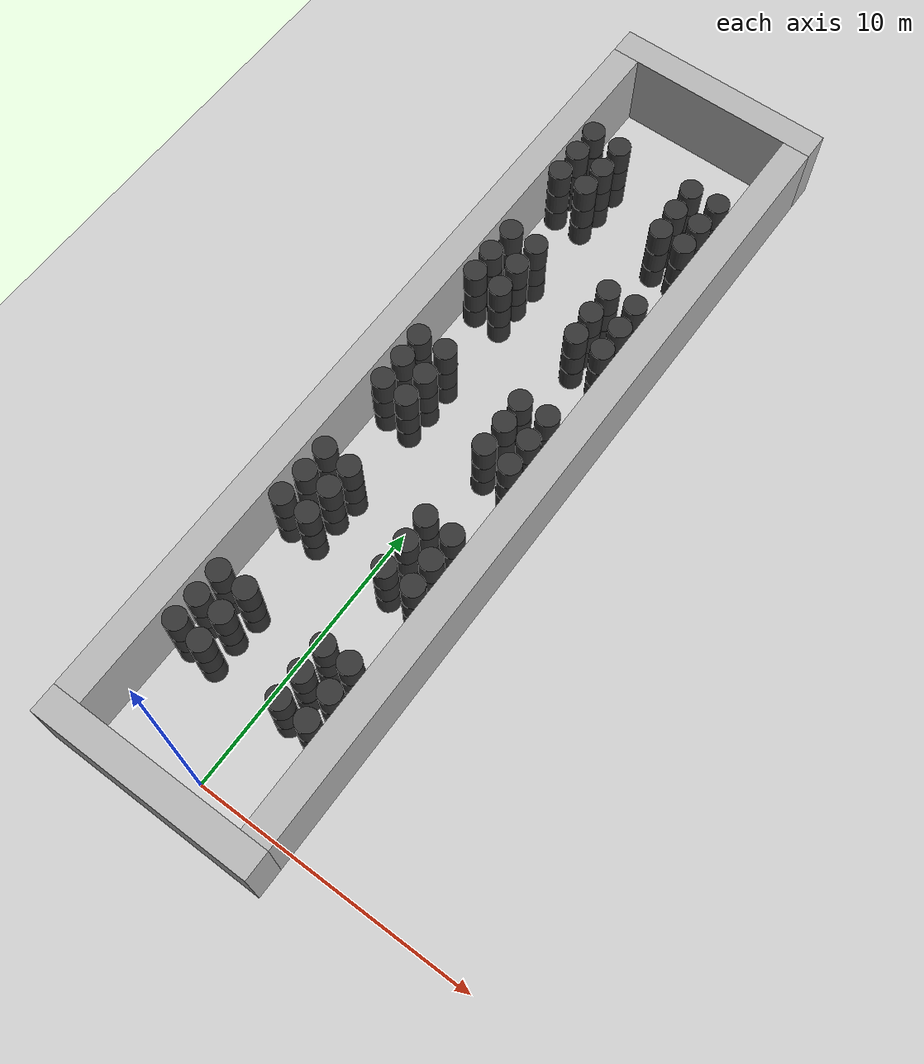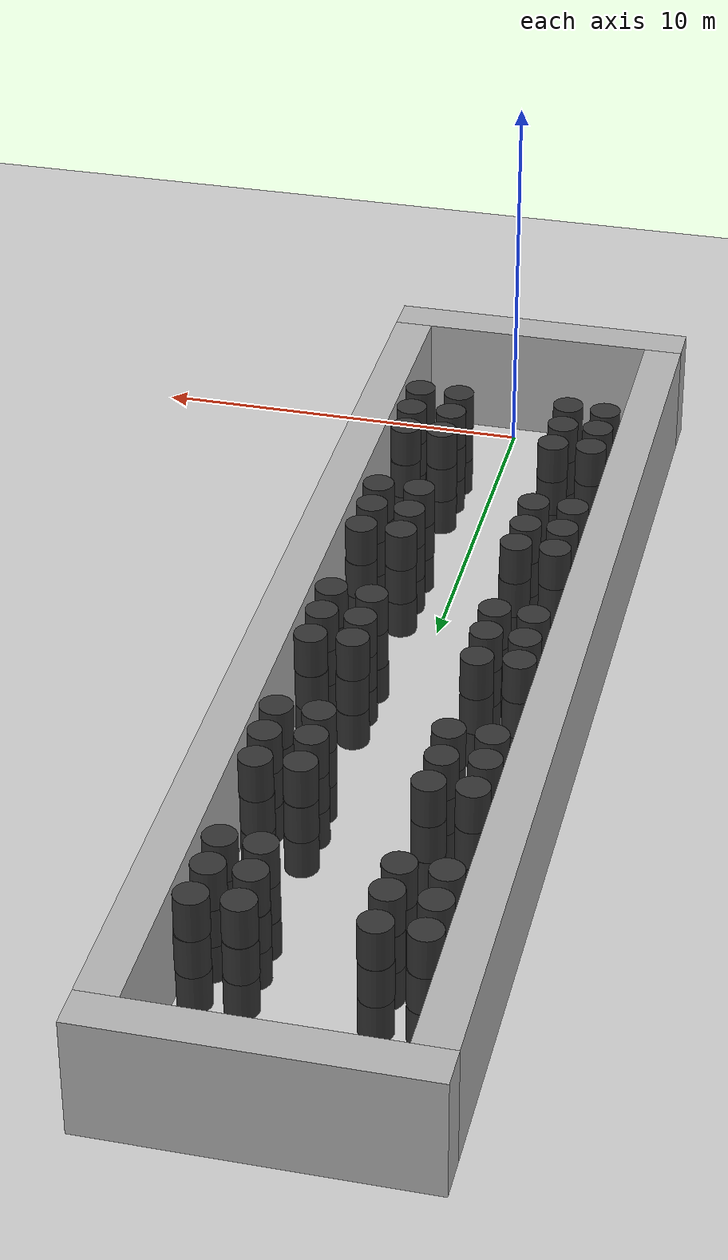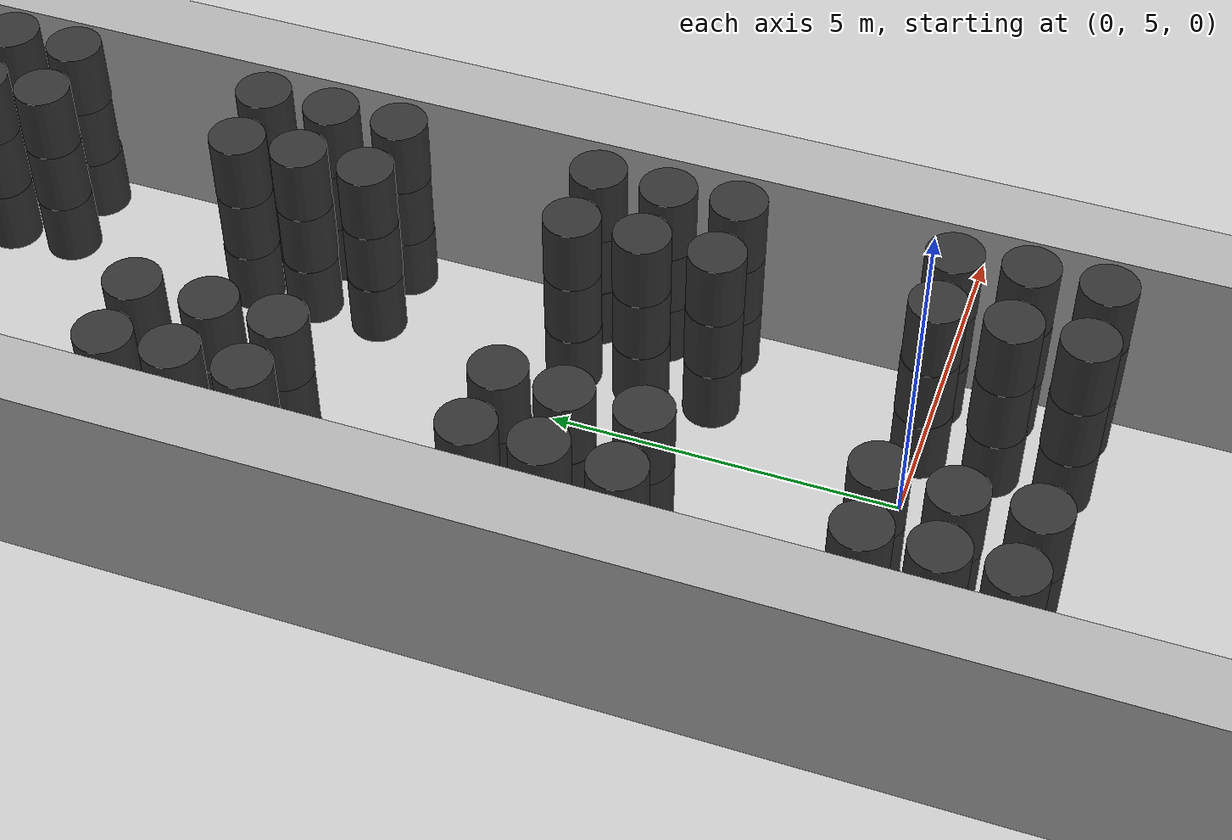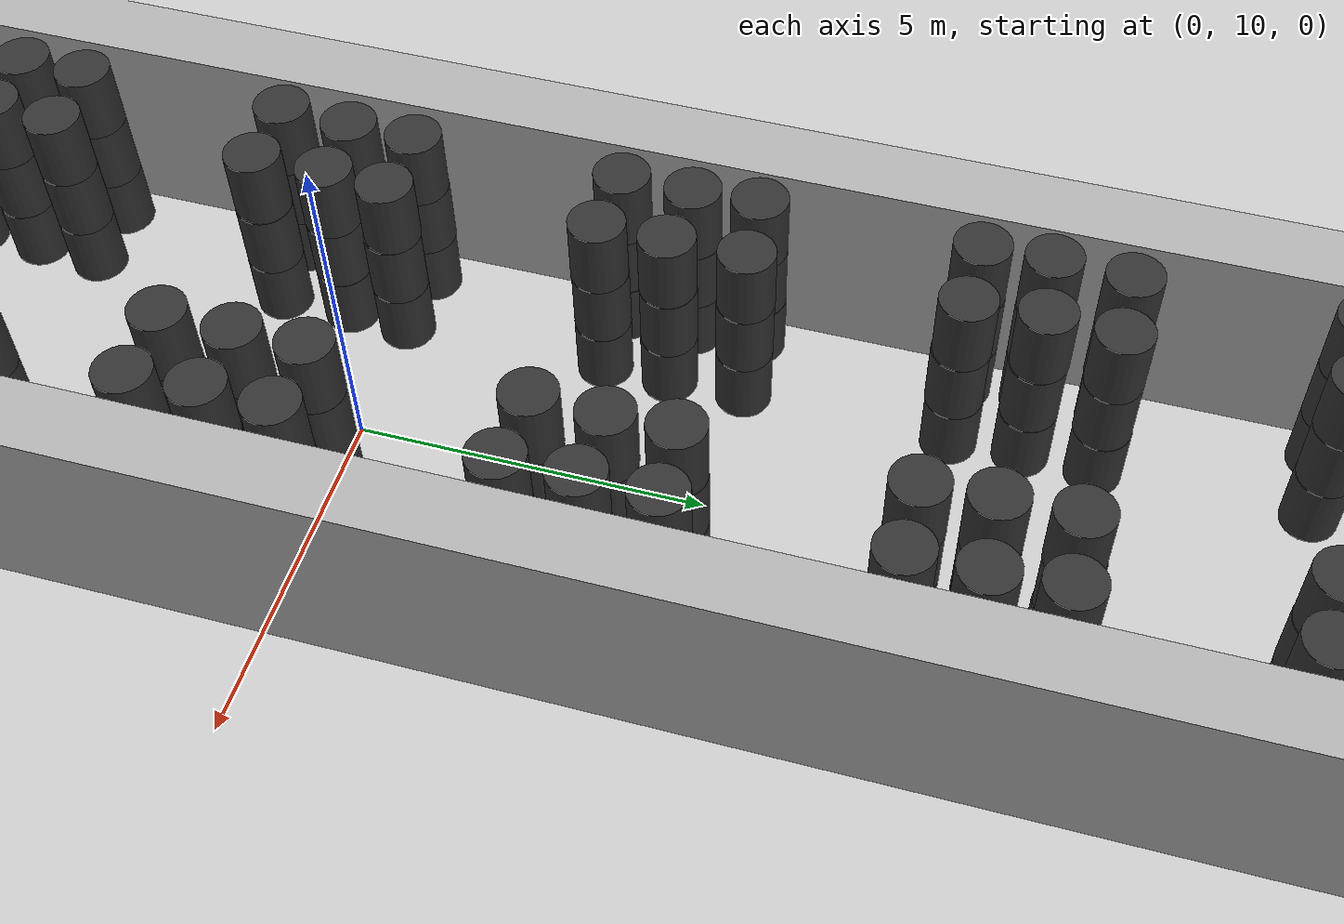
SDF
<sdf version="1.6">
 <world name="default">
  <light name="sun" type="directional">
   <cast_shadows>0</cast_shadows>
   <pose>0 0 10 0 -0 0</pose>
   <diffuse>0.8 0.8 0.8 1</diffuse>
   <specular>0.2 0.2 0.2 1</specular>
   <attenuation>
    <range>1000</range>
    <constant>0.9</constant>
    <linear>0.01</linear>
    <quadratic>0.001</quadratic>
   </attenuation>
   <direction>-0.5 0.1 -0.9</direction>
  </light>
  <include><uri>model://ground_plane</uri></include>
  <gravity>0 0 -9.8</gravity>
  <magnetic_field>6e-06 2.3e-05 -4.2e-05</magnetic_field>
  <atmosphere type="adiabatic"/>
  <physics default="0" name="default_physics" type="ode">
   <max_step_size>0.001</max_step_size>
   <real_time_factor>1</real_time_factor>
   <real_time_update_rate>1000</real_time_update_rate>
  </physics>
  <scene><ambient>0.4 0.4 0.4 1</ambient><background>0.7 0.7 0.7 1</background><shadows>0</shadows></scene>
  <spherical_coordinates>
   <surface_model>EARTH_WGS84</surface_model>
   <latitude_deg>0</latitude_deg>
   <longitude_deg>0</longitude_deg>
   <elevation>0</elevation>
   <heading_deg>0</heading_deg>
  </spherical_coordinates>
  <model name="wall_0">
   <pose frame="sim_world">-4.0 14.0 1.5 0 0 0</pose>
   <static>True</static>
   <link name="wall_0_link">
    <inertial>
     <mass>100</mass>
     <inertia>
      <ixx>0.166667</ixx>
      <ixy>0</ixy>
      <ixz>0</ixz>
      <iyy>0.166667</iyy>
      <iyz>0</iyz>
      <izz>0.166667</izz>
     </inertia>
    </inertial>
    <collision name="wall_0_collision">
     <geometry><box><size>1.0 29.0 3.0</size></box></geometry>
     <max_contacts>100</max_contacts>
    </collision>
    <visual name="wall_0_visual">
     <geometry><box><size>1.0 29.0 3.0</size></box></geometry>
     <material><ambient>0.7 0.7 0.7 1</ambient><diffuse>0.7 0.7 0.7 1</diffuse></material>
    </visual>
   </link>
  </model>
  <model name="wall_1">
   <pose frame="sim_world">3.0 14.0 1.5 0 0 0</pose>
   <static>True</static>
   <link name="wall_1_link">
    <inertial>
     <mass>100</mass>
     <inertia>
      <ixx>0.166667</ixx>
      <ixy>0</ixy>
      <ixz>0</ixz>
      <iyy>0.166667</iyy>
      <iyz>0</iyz>
      <izz>0.166667</izz>
     </inertia>
    </inertial>
    <collision name="wall_1_collision">
     <geometry><box><size>1.0 29.0 3.0</size></box></geometry>
     <max_contacts>100</max_contacts>
    </collision>
    <visual name="wall_1_visual">
     <geometry><box><size>1.0 29.0 3.0</size></box></geometry>
     <material><ambient>0.7 0.7 0.7 1</ambient><diffuse>0.7 0.7 0.7 1</diffuse></material>
    </visual>
   </link>
  </model>
  <model name="wall_2">
   <pose frame="sim_world">-0.5 -1.0 1.5 0 0 0</pose>
   <static>True</static>
   <link name="wall_2_link">
    <inertial>
     <mass>100</mass>
     <inertia>
      <ixx>0.166667</ixx>
      <ixy>0</ixy>
      <ixz>0</ixz>
      <iyy>0.166667</iyy>
      <iyz>0</iyz>
      <izz>0.166667</izz>
     </inertia>
    </inertial>
    <collision name="wall_2_collision">
     <geometry><box><size>8.0 1.0 3.0</size></box></geometry>
     <max_contacts>100</max_contacts>
    </collision>
    <visual name="wall_2_visual">
     <geometry><box><size>8.0 1.0 3.0</size></box></geometry>
     <material><ambient>0.7 0.7 0.7 1</ambient><diffuse>0.7 0.7 0.7 1</diffuse></material>
    </visual>
   </link>
  </model>
  <model name="wall_3">
   <pose frame="sim_world">-0.5 29.0 1.5 0 0 0</pose>
   <static>True</static>
   <link name="wall_3_link">
    <inertial>
     <mass>100</mass>
     <inertia>
      <ixx>0.166667</ixx>
      <ixy>0</ixy>
      <ixz>0</ixz>
      <iyy>0.166667</iyy>
      <iyz>0</iyz>
      <izz>0.166667</izz>
     </inertia>
    </inertial>
    <collision name="wall_3_collision">
     <geometry><box><size>8.0 1.0 3.0</size></box></geometry>
     <max_contacts>100</max_contacts>
    </collision>
    <visual name="wall_3_visual">
     <geometry><box><size>8.0 1.0 3.0</size></box></geometry>
     <material><ambient>0.7 0.7 0.7 1</ambient><diffuse>0.7 0.7 0.7 1</diffuse></material>
    </visual>
   </link>
  </model>
  <model name="cylinder_0">
   <pose frame="sim_world">-2.99331092369 3.04628800812 0.5 0 -0 0</pose>
   <static>True</static>
   <link name="cylinder_0_link">
    <inertial>
     <mass>100</mass>
     <inertia><ixx>0.145833</ixx><ixy>0</ixy><ixz>0</ixz><iyy>0.145833</iyy><iyz>0</iyz><izz>0.125</izz></inertia>
    </inertial>
    <collision name="cylinder_0_collision">
     <geometry><cylinder><length>1.0</length><radius>0.4</radius></cylinder></geometry>
     <max_contacts>100</max_contacts>
    </collision>
    <visual name="cylinder_0_visual">
     <geometry><cylinder><length>1.0</length><radius>0.4</radius></cylinder></geometry>
     <material><ambient>0.2 0.2 0.2 1</ambient><diffuse>0.2 0.2 0.2 1</diffuse></material>
    </visual>
   </link>
  </model>
  <model name="cylinder_1">
   <pose frame="sim_world">-2.99128336379 3.05090034139 1.5 0 -0 0</pose>
   <static>True</static>
   <link name="cylinder_1_link">
    <inertial>
     <mass>100</mass>
     <inertia><ixx>0.145833</ixx><ixy>0</ixy><ixz>0</ixz><iyy>0.145833</iyy><iyz>0</iyz><izz>0.125</izz></inertia>
    </inertial>
    <collision name="cylinder_1_collision">
     <geometry><cylinder><length>1.0</length><radius>0.4</radius></cylinder></geometry>
     <max_contacts>100</max_contacts>
    </collision>
    <visual name="cylinder_1_visual">
     <geometry><cylinder><length>1.0</length><radius>0.4</radius></cylinder></geometry>
     <material><ambient>0.2 0.2 0.2 1</ambient><diffuse>0.2 0.2 0.2 1</diffuse></material>
    </visual>
   </link>
  </model>
  <model name="cylinder_2">
   <pose frame="sim_world">-3.0080423608 3.05019383698 2.5 0 -0 0</pose>
   <static>True</static>
   <link name="cylinder_2_link">
    <inertial>
     <mass>100</mass>
     <inertia><ixx>0.145833</ixx><ixy>0</ixy><ixz>0</ixz><iyy>0.145833</iyy><iyz>0</iyz><izz>0.125</izz></inertia>
    </inertial>
    <collision name="cylinder_2_collision">
     <geometry><cylinder><length>1.0</length><radius>0.4</radius></cylinder></geometry>
     <max_contacts>100</max_contacts>
    </collision>
    <visual name="cylinder_2_visual">
     <geometry><cylinder><length>1.0</length><radius>0.4</radius></cylinder></geometry>
     <material><ambient>0.2 0.2 0.2 1</ambient><diffuse>0.2 0.2 0.2 1</diffuse></material>
    </visual>
   </link>
  </model>
  <model name="cylinder_3">
   <pose frame="sim_world">-2.97151588663 4.01085530519 0.5 0 -0 0</pose>
   <static>True</static>
   <link name="cylinder_3_link">
    <inertial>
     <mass>100</mass>
     <inertia><ixx>0.145833</ixx><ixy>0</ixy><ixz>0</ixz><iyy>0.145833</iyy><iyz>0</iyz><izz>0.125</izz></inertia>
    </inertial>
    <collision name="cylinder_3_collision">
     <geometry><cylinder><length>1.0</length><radius>0.4</radius></cylinder></geometry>
     <max_contacts>100</max_contacts>
    </collision>
    <visual name="cylinder_3_visual">
     <geometry><cylinder><length>1.0</length><radius>0.4</radius></cylinder></geometry>
     <material><ambient>0.2 0.2 0.2 1</ambient><diffuse>0.2 0.2 0.2 1</diffuse></material>
    </visual>
   </link>
  </model>
  <model name="cylinder_4">
   <pose frame="sim_world">-2.97826024934 4.00481571654 1.5 0 -0 0</pose>
   <static>True</static>
   <link name="cylinder_4_link">
    <inertial>
     <mass>100</mass>
     <inertia><ixx>0.145833</ixx><ixy>0</ixy><ixz>0</ixz><iyy>0.145833</iyy><iyz>0</iyz><izz>0.125</izz></inertia>
    </inertial>
    <collision name="cylinder_4_collision">
     <geometry><cylinder><length>1.0</length><radius>0.4</radius></cylinder></geometry>
     <max_contacts>100</max_contacts>
    </collision>
    <visual name="cylinder_4_visual">
     <geometry><cylinder><length>1.0</length><radius>0.4</radius></cylinder></geometry>
     <material><ambient>0.2 0.2 0.2 1</ambient><diffuse>0.2 0.2 0.2 1</diffuse></material>
    </visual>
   </link>
  </model>
  <model name="cylinder_5">
   <pose frame="sim_world">-2.97621861829 4.0005700455 2.5 0 -0 0</pose>
   <static>True</static>
   <link name="cylinder_5_link">
    <inertial>
     <mass>100</mass>
     <inertia><ixx>0.145833</ixx><ixy>0</ixy><ixz>0</ixz><iyy>0.145833</iyy><iyz>0</iyz><izz>0.125</izz></inertia>
    </inertial>
    <collision name="cylinder_5_collision">
     <geometry><cylinder><length>1.0</length><radius>0.4</radius></cylinder></geometry>
     <max_contacts>100</max_contacts>
    </collision>
    <visual name="cylinder_5_visual">
     <geometry><cylinder><length>1.0</length><radius>0.4</radius></cylinder></geometry>
     <material><ambient>0.2 0.2 0.2 1</ambient><diffuse>0.2 0.2 0.2 1</diffuse></material>
    </visual>
   </link>
  </model>
  <model name="cylinder_6">
   <pose frame="sim_world">-2.97489112418 4.94994942638 0.5 0 -0 0</pose>
   <static>True</static>
   <link name="cylinder_6_link">
    <inertial>
     <mass>100</mass>
     <inertia><ixx>0.145833</ixx><ixy>0</ixy><ixz>0</ixz><iyy>0.145833</iyy><iyz>0</iyz><izz>0.125</izz></inertia>
    </inertial>
    <collision name="cylinder_6_collision">
     <geometry><cylinder><length>1.0</length><radius>0.4</radius></cylinder></geometry>
     <max_contacts>100</max_contacts>
    </collision>
    <visual name="cylinder_6_visual">
     <geometry><cylinder><length>1.0</length><radius>0.4</radius></cylinder></geometry>
     <material><ambient>0.2 0.2 0.2 1</ambient><diffuse>0.2 0.2 0.2 1</diffuse></material>
    </visual>
   </link>
  </model>
  <model name="cylinder_7">
   <pose frame="sim_world">-2.96457506904 4.95433120491 1.5 0 -0 0</pose>
   <static>True</static>
   <link name="cylinder_7_link">
    <inertial>
     <mass>100</mass>
     <inertia><ixx>0.145833</ixx><ixy>0</ixy><ixz>0</ixz><iyy>0.145833</iyy><iyz>0</iyz><izz>0.125</izz></inertia>
    </inertial>
    <collision name="cylinder_7_collision">
     <geometry><cylinder><length>1.0</length><radius>0.4</radius></cylinder></geometry>
     <max_contacts>100</max_contacts>
    </collision>
    <visual name="cylinder_7_visual">
     <geometry><cylinder><length>1.0</length><radius>0.4</radius></cylinder></geometry>
     <material><ambient>0.2 0.2 0.2 1</ambient><diffuse>0.2 0.2 0.2 1</diffuse></material>
    </visual>
   </link>
  </model>
  <model name="cylinder_8">
   <pose frame="sim_world">-2.96331615626 4.95802939447 2.5 0 -0 0</pose>
   <static>True</static>
   <link name="cylinder_8_link">
    <inertial>
     <mass>100</mass>
     <inertia><ixx>0.145833</ixx><ixy>0</ixy><ixz>0</ixz><iyy>0.145833</iyy><iyz>0</iyz><izz>0.125</izz></inertia>
    </inertial>
    <collision name="cylinder_8_collision">
     <geometry><cylinder><length>1.0</length><radius>0.4</radius></cylinder></geometry>
     <max_contacts>100</max_contacts>
    </collision>
    <visual name="cylinder_8_visual">
     <geometry><cylinder><length>1.0</length><radius>0.4</radius></cylinder></geometry>
     <material><ambient>0.2 0.2 0.2 1</ambient><diffuse>0.2 0.2 0.2 1</diffuse></material>
    </visual>
   </link>
  </model>
  <model name="cylinder_9">
   <pose frame="sim_world">-3.02466633321 8.0019167953 0.5 0 -0 0</pose>
   <static>True</static>
   <link name="cylinder_9_link">
    <inertial>
     <mass>100</mass>
     <inertia><ixx>0.145833</ixx><ixy>0</ixy><ixz>0</ixz><iyy>0.145833</iyy><iyz>0</iyz><izz>0.125</izz></inertia>
    </inertial>
    <collision name="cylinder_9_collision">
     <geometry><cylinder><length>1.0</length><radius>0.4</radius></cylinder></geometry>
     <max_contacts>100</max_contacts>
    </collision>
    <visual name="cylinder_9_visual">
     <geometry><cylinder><length>1.0</length><radius>0.4</radius></cylinder></geometry>
     <material><ambient>0.2 0.2 0.2 1</ambient><diffuse>0.2 0.2 0.2 1</diffuse></material>
    </visual>
   </link>
  </model>
  <model name="cylinder_10">
   <pose frame="sim_world">-3.0239855596 8.01013254635 1.5 0 -0 0</pose>
   <static>True</static>
   <link name="cylinder_10_link">
    <inertial>
     <mass>100</mass>
     <inertia><ixx>0.145833</ixx><ixy>0</ixy><ixz>0</ixz><iyy>0.145833</iyy><iyz>0</iyz><izz>0.125</izz></inertia>
    </inertial>
    <collision name="cylinder_10_collision">
     <geometry><cylinder><length>1.0</length><radius>0.4</radius></cylinder></geometry>
     <max_contacts>100</max_contacts>
    </collision>
    <visual name="cylinder_10_visual">
     <geometry><cylinder><length>1.0</length><radius>0.4</radius></cylinder></geometry>
     <material><ambient>0.2 0.2 0.2 1</ambient><diffuse>0.2 0.2 0.2 1</diffuse></material>
    </visual>
   </link>
  </model>
  <model name="cylinder_11">
   <pose frame="sim_world">-3.03300908969 8.00423963865 2.5 0 -0 0</pose>
   <static>True</static>
   <link name="cylinder_11_link">
    <inertial>
     <mass>100</mass>
     <inertia><ixx>0.145833</ixx><ixy>0</ixy><ixz>0</ixz><iyy>0.145833</iyy><iyz>0</iyz><izz>0.125</izz></inertia>
    </inertial>
    <collision name="cylinder_11_collision">
     <geometry><cylinder><length>1.0</length><radius>0.4</radius></cylinder></geometry>
     <max_contacts>100</max_contacts>
    </collision>
    <visual name="cylinder_11_visual">
     <geometry><cylinder><length>1.0</length><radius>0.4</radius></cylinder></geometry>
     <material><ambient>0.2 0.2 0.2 1</ambient><diffuse>0.2 0.2 0.2 1</diffuse></material>
    </visual>
   </link>
  </model>
  <model name="cylinder_12">
   <pose frame="sim_world">-2.96160246649 9.04521391994 0.5 0 -0 0</pose>
   <static>True</static>
   <link name="cylinder_12_link">
    <inertial>
     <mass>100</mass>
     <inertia><ixx>0.145833</ixx><ixy>0</ixy><ixz>0</ixz><iyy>0.145833</iyy><iyz>0</iyz><izz>0.125</izz></inertia>
    </inertial>
    <collision name="cylinder_12_collision">
     <geometry><cylinder><length>1.0</length><radius>0.4</radius></cylinder></geometry>
     <max_contacts>100</max_contacts>
    </collision>
    <visual name="cylinder_12_visual">
     <geometry><cylinder><length>1.0</length><radius>0.4</radius></cylinder></geometry>
     <material><ambient>0.2 0.2 0.2 1</ambient><diffuse>0.2 0.2 0.2 1</diffuse></material>
    </visual>
   </link>
  </model>
  <model name="cylinder_13">
   <pose frame="sim_world">-2.96980164215 9.03584769395 1.5 0 -0 0</pose>
   <static>True</static>
   <link name="cylinder_13_link">
    <inertial>
     <mass>100</mass>
     <inertia><ixx>0.145833</ixx><ixy>0</ixy><ixz>0</ixz><iyy>0.145833</iyy><iyz>0</iyz><izz>0.125</izz></inertia>
    </inertial>
    <collision name="cylinder_13_collision">
     <geometry><cylinder><length>1.0</length><radius>0.4</radius></cylinder></geometry>
     <max_contacts>100</max_contacts>
    </collision>
    <visual name="cylinder_13_visual">
     <geometry><cylinder><length>1.0</length><radius>0.4</radius></cylinder></geometry>
     <material><ambient>0.2 0.2 0.2 1</ambient><diffuse>0.2 0.2 0.2 1</diffuse></material>
    </visual>
   </link>
  </model>
  <model name="cylinder_14">
   <pose frame="sim_world">-2.96016807215 9.04546093262 2.5 0 -0 0</pose>
   <static>True</static>
   <link name="cylinder_14_link">
    <inertial>
     <mass>100</mass>
     <inertia><ixx>0.145833</ixx><ixy>0</ixy><ixz>0</ixz><iyy>0.145833</iyy><iyz>0</iyz><izz>0.125</izz></inertia>
    </inertial>
    <collision name="cylinder_14_collision">
     <geometry><cylinder><length>1.0</length><radius>0.4</radius></cylinder></geometry>
     <max_contacts>100</max_contacts>
    </collision>
    <visual name="cylinder_14_visual">
     <geometry><cylinder><length>1.0</length><radius>0.4</radius></cylinder></geometry>
     <material><ambient>0.2 0.2 0.2 1</ambient><diffuse>0.2 0.2 0.2 1</diffuse></material>
    </visual>
   </link>
  </model>
  <model name="cylinder_15">
   <pose frame="sim_world">-2.95974717272 9.99762335335 0.5 0 -0 0</pose>
   <static>True</static>
   <link name="cylinder_15_link">
    <inertial>
     <mass>100</mass>
     <inertia><ixx>0.145833</ixx><ixy>0</ixy><ixz>0</ixz><iyy>0.145833</iyy><iyz>0</iyz><izz>0.125</izz></inertia>
    </inertial>
    <collision name="cylinder_15_collision">
     <geometry><cylinder><length>1.0</length><radius>0.4</radius></cylinder></geometry>
     <max_contacts>100</max_contacts>
    </collision>
    <visual name="cylinder_15_visual">
     <geometry><cylinder><length>1.0</length><radius>0.4</radius></cylinder></geometry>
     <material><ambient>0.2 0.2 0.2 1</ambient><diffuse>0.2 0.2 0.2 1</diffuse></material>
    </visual>
   </link>
  </model>
  <model name="cylinder_16">
   <pose frame="sim_world">-2.96733454405 10.0077599874 1.5 0 -0 0</pose>
   <static>True</static>
   <link name="cylinder_16_link">
    <inertial>
     <mass>100</mass>
     <inertia><ixx>0.145833</ixx><ixy>0</ixy><ixz>0</ixz><iyy>0.145833</iyy><iyz>0</iyz><izz>0.125</izz></inertia>
    </inertial>
    <collision name="cylinder_16_collision">
     <geometry><cylinder><length>1.0</length><radius>0.4</radius></cylinder></geometry>
     <max_contacts>100</max_contacts>
    </collision>
    <visual name="cylinder_16_visual">
     <geometry><cylinder><length>1.0</length><radius>0.4</radius></cylinder></geometry>
     <material><ambient>0.2 0.2 0.2 1</ambient><diffuse>0.2 0.2 0.2 1</diffuse></material>
    </visual>
   </link>
  </model>
  <model name="cylinder_17">
   <pose frame="sim_world">-2.9538205058 10.0074615674 2.5 0 -0 0</pose>
   <static>True</static>
   <link name="cylinder_17_link">
    <inertial>
     <mass>100</mass>
     <inertia><ixx>0.145833</ixx><ixy>0</ixy><ixz>0</ixz><iyy>0.145833</iyy><iyz>0</iyz><izz>0.125</izz></inertia>
    </inertial>
    <collision name="cylinder_17_collision">
     <geometry><cylinder><length>1.0</length><radius>0.4</radius></cylinder></geometry>
     <max_contacts>100</max_contacts>
    </collision>
    <visual name="cylinder_17_visual">
     <geometry><cylinder><length>1.0</length><radius>0.4</radius></cylinder></geometry>
     <material><ambient>0.2 0.2 0.2 1</ambient><diffuse>0.2 0.2 0.2 1</diffuse></material>
    </visual>
   </link>
  </model>
  <model name="cylinder_18">
   <pose frame="sim_world">-2.99630284277 13.0216252734 0.5 0 -0 0</pose>
   <static>True</static>
   <link name="cylinder_18_link">
    <inertial>
     <mass>100</mass>
     <inertia><ixx>0.145833</ixx><ixy>0</ixy><ixz>0</ixz><iyy>0.145833</iyy><iyz>0</iyz><izz>0.125</izz></inertia>
    </inertial>
    <collision name="cylinder_18_collision">
     <geometry><cylinder><length>1.0</length><radius>0.4</radius></cylinder></geometry>
     <max_contacts>100</max_contacts>
    </collision>
    <visual name="cylinder_18_visual">
     <geometry><cylinder><length>1.0</length><radius>0.4</radius></cylinder></geometry>
     <material><ambient>0.2 0.2 0.2 1</ambient><diffuse>0.2 0.2 0.2 1</diffuse></material>
    </visual>
   </link>
  </model>
  <model name="cylinder_19">
   <pose frame="sim_world">-3.01050325647 13.0122026184 1.5 0 -0 0</pose>
   <static>True</static>
   <link name="cylinder_19_link">
    <inertial>
     <mass>100</mass>
     <inertia><ixx>0.145833</ixx><ixy>0</ixy><ixz>0</ixz><iyy>0.145833</iyy><iyz>0</iyz><izz>0.125</izz></inertia>
    </inertial>
    <collision name="cylinder_19_collision">
     <geometry><cylinder><length>1.0</length><radius>0.4</radius></cylinder></geometry>
     <max_contacts>100</max_contacts>
    </collision>
    <visual name="cylinder_19_visual">
     <geometry><cylinder><length>1.0</length><radius>0.4</radius></cylinder></geometry>
     <material><ambient>0.2 0.2 0.2 1</ambient><diffuse>0.2 0.2 0.2 1</diffuse></material>
    </visual>
   </link>
  </model>
  <model name="cylinder_20">
   <pose frame="sim_world">-2.99424971212 13.0228038659 2.5 0 -0 0</pose>
   <static>True</static>
   <link name="cylinder_20_link">
    <inertial>
     <mass>100</mass>
     <inertia><ixx>0.145833</ixx><ixy>0</ixy><ixz>0</ixz><iyy>0.145833</iyy><iyz>0</iyz><izz>0.125</izz></inertia>
    </inertial>
    <collision name="cylinder_20_collision">
     <geometry><cylinder><length>1.0</length><radius>0.4</radius></cylinder></geometry>
     <max_contacts>100</max_contacts>
    </collision>
    <visual name="cylinder_20_visual">
     <geometry><cylinder><length>1.0</length><radius>0.4</radius></cylinder></geometry>
     <material><ambient>0.2 0.2 0.2 1</ambient><diffuse>0.2 0.2 0.2 1</diffuse></material>
    </visual>
   </link>
  </model>
  <model name="cylinder_21">
   <pose frame="sim_world">-2.98432138656 14.0504166469 0.5 0 -0 0</pose>
   <static>True</static>
   <link name="cylinder_21_link">
    <inertial>
     <mass>100</mass>
     <inertia><ixx>0.145833</ixx><ixy>0</ixy><ixz>0</ixz><iyy>0.145833</iyy><iyz>0</iyz><izz>0.125</izz></inertia>
    </inertial>
    <collision name="cylinder_21_collision">
     <geometry><cylinder><length>1.0</length><radius>0.4</radius></cylinder></geometry>
     <max_contacts>100</max_contacts>
    </collision>
    <visual name="cylinder_21_visual">
     <geometry><cylinder><length>1.0</length><radius>0.4</radius></cylinder></geometry>
     <material><ambient>0.2 0.2 0.2 1</ambient><diffuse>0.2 0.2 0.2 1</diffuse></material>
    </visual>
   </link>
  </model>
  <model name="cylinder_22">
   <pose frame="sim_world">-2.98310022397 14.0452732466 1.5 0 -0 0</pose>
   <static>True</static>
   <link name="cylinder_22_link">
    <inertial>
     <mass>100</mass>
     <inertia><ixx>0.145833</ixx><ixy>0</ixy><ixz>0</ixz><iyy>0.145833</iyy><iyz>0</iyz><izz>0.125</izz></inertia>
    </inertial>
    <collision name="cylinder_22_collision">
     <geometry><cylinder><length>1.0</length><radius>0.4</radius></cylinder></geometry>
     <max_contacts>100</max_contacts>
    </collision>
    <visual name="cylinder_22_visual">
     <geometry><cylinder><length>1.0</length><radius>0.4</radius></cylinder></geometry>
     <material><ambient>0.2 0.2 0.2 1</ambient><diffuse>0.2 0.2 0.2 1</diffuse></material>
    </visual>
   </link>
  </model>
  <model name="cylinder_23">
   <pose frame="sim_world">-2.98236017431 14.0354608389 2.5 0 -0 0</pose>
   <static>True</static>
   <link name="cylinder_23_link">
    <inertial>
     <mass>100</mass>
     <inertia><ixx>0.145833</ixx><ixy>0</ixy><ixz>0</ixz><iyy>0.145833</iyy><iyz>0</iyz><izz>0.125</izz></inertia>
    </inertial>
    <collision name="cylinder_23_collision">
     <geometry><cylinder><length>1.0</length><radius>0.4</radius></cylinder></geometry>
     <max_contacts>100</max_contacts>
    </collision>
    <visual name="cylinder_23_visual">
     <geometry><cylinder><length>1.0</length><radius>0.4</radius></cylinder></geometry>
     <material><ambient>0.2 0.2 0.2 1</ambient><diffuse>0.2 0.2 0.2 1</diffuse></material>
    </visual>
   </link>
  </model>
  <model name="cylinder_24">
   <pose frame="sim_world">-3.042406147 14.9754270639 0.5 0 -0 0</pose>
   <static>True</static>
   <link name="cylinder_24_link">
    <inertial>
     <mass>100</mass>
     <inertia><ixx>0.145833</ixx><ixy>0</ixy><ixz>0</ixz><iyy>0.145833</iyy><iyz>0</iyz><izz>0.125</izz></inertia>
    </inertial>
    <collision name="cylinder_24_collision">
     <geometry><cylinder><length>1.0</length><radius>0.4</radius></cylinder></geometry>
     <max_contacts>100</max_contacts>
    </collision>
    <visual name="cylinder_24_visual">
     <geometry><cylinder><length>1.0</length><radius>0.4</radius></cylinder></geometry>
     <material><ambient>0.2 0.2 0.2 1</ambient><diffuse>0.2 0.2 0.2 1</diffuse></material>
    </visual>
   </link>
  </model>
  <model name="cylinder_25">
   <pose frame="sim_world">-3.04206244545 14.9629978575 1.5 0 -0 0</pose>
   <static>True</static>
   <link name="cylinder_25_link">
    <inertial>
     <mass>100</mass>
     <inertia><ixx>0.145833</ixx><ixy>0</ixy><ixz>0</ixz><iyy>0.145833</iyy><iyz>0</iyz><izz>0.125</izz></inertia>
    </inertial>
    <collision name="cylinder_25_collision">
     <geometry><cylinder><length>1.0</length><radius>0.4</radius></cylinder></geometry>
     <max_contacts>100</max_contacts>
    </collision>
    <visual name="cylinder_25_visual">
     <geometry><cylinder><length>1.0</length><radius>0.4</radius></cylinder></geometry>
     <material><ambient>0.2 0.2 0.2 1</ambient><diffuse>0.2 0.2 0.2 1</diffuse></material>
    </visual>
   </link>
  </model>
  <model name="cylinder_26">
   <pose frame="sim_world">-3.03224205885 14.9648059669 2.5 0 -0 0</pose>
   <static>True</static>
   <link name="cylinder_26_link">
    <inertial>
     <mass>100</mass>
     <inertia><ixx>0.145833</ixx><ixy>0</ixy><ixz>0</ixz><iyy>0.145833</iyy><iyz>0</iyz><izz>0.125</izz></inertia>
    </inertial>
    <collision name="cylinder_26_collision">
     <geometry><cylinder><length>1.0</length><radius>0.4</radius></cylinder></geometry>
     <max_contacts>100</max_contacts>
    </collision>
    <visual name="cylinder_26_visual">
     <geometry><cylinder><length>1.0</length><radius>0.4</radius></cylinder></geometry>
     <material><ambient>0.2 0.2 0.2 1</ambient><diffuse>0.2 0.2 0.2 1</diffuse></material>
    </visual>
   </link>
  </model>
  <model name="cylinder_27">
   <pose frame="sim_world">-3.00701187167 18.023755769 0.5 0 -0 0</pose>
   <static>True</static>
   <link name="cylinder_27_link">
    <inertial>
     <mass>100</mass>
     <inertia><ixx>0.145833</ixx><ixy>0</ixy><ixz>0</ixz><iyy>0.145833</iyy><iyz>0</iyz><izz>0.125</izz></inertia>
    </inertial>
    <collision name="cylinder_27_collision">
     <geometry><cylinder><length>1.0</length><radius>0.4</radius></cylinder></geometry>
     <max_contacts>100</max_contacts>
    </collision>
    <visual name="cylinder_27_visual">
     <geometry><cylinder><length>1.0</length><radius>0.4</radius></cylinder></geometry>
     <material><ambient>0.2 0.2 0.2 1</ambient><diffuse>0.2 0.2 0.2 1</diffuse></material>
    </visual>
   </link>
  </model>
  <model name="cylinder_28">
   <pose frame="sim_world">-3.00248028948 18.0226749165 1.5 0 -0 0</pose>
   <static>True</static>
   <link name="cylinder_28_link">
    <inertial>
     <mass>100</mass>
     <inertia><ixx>0.145833</ixx><ixy>0</ixy><ixz>0</ixz><iyy>0.145833</iyy><iyz>0</iyz><izz>0.125</izz></inertia>
    </inertial>
    <collision name="cylinder_28_collision">
     <geometry><cylinder><length>1.0</length><radius>0.4</radius></cylinder></geometry>
     <max_contacts>100</max_contacts>
    </collision>
    <visual name="cylinder_28_visual">
     <geometry><cylinder><length>1.0</length><radius>0.4</radius></cylinder></geometry>
     <material><ambient>0.2 0.2 0.2 1</ambient><diffuse>0.2 0.2 0.2 1</diffuse></material>
    </visual>
   </link>
  </model>
  <model name="cylinder_29">
   <pose frame="sim_world">-3.00870383393 18.0157991154 2.5 0 -0 0</pose>
   <static>True</static>
   <link name="cylinder_29_link">
    <inertial>
     <mass>100</mass>
     <inertia><ixx>0.145833</ixx><ixy>0</ixy><ixz>0</ixz><iyy>0.145833</iyy><iyz>0</iyz><izz>0.125</izz></inertia>
    </inertial>
    <collision name="cylinder_29_collision">
     <geometry><cylinder><length>1.0</length><radius>0.4</radius></cylinder></geometry>
     <max_contacts>100</max_contacts>
    </collision>
    <visual name="cylinder_29_visual">
     <geometry><cylinder><length>1.0</length><radius>0.4</radius></cylinder></geometry>
     <material><ambient>0.2 0.2 0.2 1</ambient><diffuse>0.2 0.2 0.2 1</diffuse></material>
    </visual>
   </link>
  </model>
  <model name="cylinder_30">
   <pose frame="sim_world">-3.03980811727 18.9614411124 0.5 0 -0 0</pose>
   <static>True</static>
   <link name="cylinder_30_link">
    <inertial>
     <mass>100</mass>
     <inertia><ixx>0.145833</ixx><ixy>0</ixy><ixz>0</ixz><iyy>0.145833</iyy><iyz>0</iyz><izz>0.125</izz></inertia>
    </inertial>
    <collision name="cylinder_30_collision">
     <geometry><cylinder><length>1.0</length><radius>0.4</radius></cylinder></geometry>
     <max_contacts>100</max_contacts>
    </collision>
    <visual name="cylinder_30_visual">
     <geometry><cylinder><length>1.0</length><radius>0.4</radius></cylinder></geometry>
     <material><ambient>0.2 0.2 0.2 1</ambient><diffuse>0.2 0.2 0.2 1</diffuse></material>
    </visual>
   </link>
  </model>
  <model name="cylinder_31">
   <pose frame="sim_world">-3.03408151154 18.9624144078 1.5 0 -0 0</pose>
   <static>True</static>
   <link name="cylinder_31_link">
    <inertial>
     <mass>100</mass>
     <inertia><ixx>0.145833</ixx><ixy>0</ixy><ixz>0</ixz><iyy>0.145833</iyy><iyz>0</iyz><izz>0.125</izz></inertia>
    </inertial>
    <collision name="cylinder_31_collision">
     <geometry><cylinder><length>1.0</length><radius>0.4</radius></cylinder></geometry>
     <max_contacts>100</max_contacts>
    </collision>
    <visual name="cylinder_31_visual">
     <geometry><cylinder><length>1.0</length><radius>0.4</radius></cylinder></geometry>
     <material><ambient>0.2 0.2 0.2 1</ambient><diffuse>0.2 0.2 0.2 1</diffuse></material>
    </visual>
   </link>
  </model>
  <model name="cylinder_32">
   <pose frame="sim_world">-3.04690763 18.9666969515 2.5 0 -0 0</pose>
   <static>True</static>
   <link name="cylinder_32_link">
    <inertial>
     <mass>100</mass>
     <inertia><ixx>0.145833</ixx><ixy>0</ixy><ixz>0</ixz><iyy>0.145833</iyy><iyz>0</iyz><izz>0.125</izz></inertia>
    </inertial>
    <collision name="cylinder_32_collision">
     <geometry><cylinder><length>1.0</length><radius>0.4</radius></cylinder></geometry>
     <max_contacts>100</max_contacts>
    </collision>
    <visual name="cylinder_32_visual">
     <geometry><cylinder><length>1.0</length><radius>0.4</radius></cylinder></geometry>
     <material><ambient>0.2 0.2 0.2 1</ambient><diffuse>0.2 0.2 0.2 1</diffuse></material>
    </visual>
   </link>
  </model>
  <model name="cylinder_33">
   <pose frame="sim_world">-2.99564388703 20.0531173185 0.5 0 -0 0</pose>
   <static>True</static>
   <link name="cylinder_33_link">
    <inertial>
     <mass>100</mass>
     <inertia><ixx>0.145833</ixx><ixy>0</ixy><ixz>0</ixz><iyy>0.145833</iyy><iyz>0</iyz><izz>0.125</izz></inertia>
    </inertial>
    <collision name="cylinder_33_collision">
     <geometry><cylinder><length>1.0</length><radius>0.4</radius></cylinder></geometry>
     <max_contacts>100</max_contacts>
    </collision>
    <visual name="cylinder_33_visual">
     <geometry><cylinder><length>1.0</length><radius>0.4</radius></cylinder></geometry>
     <material><ambient>0.2 0.2 0.2 1</ambient><diffuse>0.2 0.2 0.2 1</diffuse></material>
    </visual>
   </link>
  </model>
  <model name="cylinder_34">
   <pose frame="sim_world">-2.99322209723 20.0410647307 1.5 0 -0 0</pose>
   <static>True</static>
   <link name="cylinder_34_link">
    <inertial>
     <mass>100</mass>
     <inertia><ixx>0.145833</ixx><ixy>0</ixy><ixz>0</ixz><iyy>0.145833</iyy><iyz>0</iyz><izz>0.125</izz></inertia>
    </inertial>
    <collision name="cylinder_34_collision">
     <geometry><cylinder><length>1.0</length><radius>0.4</radius></cylinder></geometry>
     <max_contacts>100</max_contacts>
    </collision>
    <visual name="cylinder_34_visual">
     <geometry><cylinder><length>1.0</length><radius>0.4</radius></cylinder></geometry>
     <material><ambient>0.2 0.2 0.2 1</ambient><diffuse>0.2 0.2 0.2 1</diffuse></material>
    </visual>
   </link>
  </model>
  <model name="cylinder_35">
   <pose frame="sim_world">-2.99016088027 20.0374575243 2.5 0 -0 0</pose>
   <static>True</static>
   <link name="cylinder_35_link">
    <inertial>
     <mass>100</mass>
     <inertia><ixx>0.145833</ixx><ixy>0</ixy><ixz>0</ixz><iyy>0.145833</iyy><iyz>0</iyz><izz>0.125</izz></inertia>
    </inertial>
    <collision name="cylinder_35_collision">
     <geometry><cylinder><length>1.0</length><radius>0.4</radius></cylinder></geometry>
     <max_contacts>100</max_contacts>
    </collision>
    <visual name="cylinder_35_visual">
     <geometry><cylinder><length>1.0</length><radius>0.4</radius></cylinder></geometry>
     <material><ambient>0.2 0.2 0.2 1</ambient><diffuse>0.2 0.2 0.2 1</diffuse></material>
    </visual>
   </link>
  </model>
  <model name="cylinder_36">
   <pose frame="sim_world">-3.05348859282 23.0096410358 0.5 0 -0 0</pose>
   <static>True</static>
   <link name="cylinder_36_link">
    <inertial>
     <mass>100</mass>
     <inertia><ixx>0.145833</ixx><ixy>0</ixy><ixz>0</ixz><iyy>0.145833</iyy><iyz>0</iyz><izz>0.125</izz></inertia>
    </inertial>
    <collision name="cylinder_36_collision">
     <geometry><cylinder><length>1.0</length><radius>0.4</radius></cylinder></geometry>
     <max_contacts>100</max_contacts>
    </collision>
    <visual name="cylinder_36_visual">
     <geometry><cylinder><length>1.0</length><radius>0.4</radius></cylinder></geometry>
     <material><ambient>0.2 0.2 0.2 1</ambient><diffuse>0.2 0.2 0.2 1</diffuse></material>
    </visual>
   </link>
  </model>
  <model name="cylinder_37">
   <pose frame="sim_world">-3.05013833795 23.0075990019 1.5 0 -0 0</pose>
   <static>True</static>
   <link name="cylinder_37_link">
    <inertial>
     <mass>100</mass>
     <inertia><ixx>0.145833</ixx><ixy>0</ixy><ixz>0</ixz><iyy>0.145833</iyy><iyz>0</iyz><izz>0.125</izz></inertia>
    </inertial>
    <collision name="cylinder_37_collision">
     <geometry><cylinder><length>1.0</length><radius>0.4</radius></cylinder></geometry>
     <max_contacts>100</max_contacts>
    </collision>
    <visual name="cylinder_37_visual">
     <geometry><cylinder><length>1.0</length><radius>0.4</radius></cylinder></geometry>
     <material><ambient>0.2 0.2 0.2 1</ambient><diffuse>0.2 0.2 0.2 1</diffuse></material>
    </visual>
   </link>
  </model>
  <model name="cylinder_38">
   <pose frame="sim_world">-3.04901959713 23.0092645543 2.5 0 -0 0</pose>
   <static>True</static>
   <link name="cylinder_38_link">
    <inertial>
     <mass>100</mass>
     <inertia><ixx>0.145833</ixx><ixy>0</ixy><ixz>0</ixz><iyy>0.145833</iyy><iyz>0</iyz><izz>0.125</izz></inertia>
    </inertial>
    <collision name="cylinder_38_collision">
     <geometry><cylinder><length>1.0</length><radius>0.4</radius></cylinder></geometry>
     <max_contacts>100</max_contacts>
    </collision>
    <visual name="cylinder_38_visual">
     <geometry><cylinder><length>1.0</length><radius>0.4</radius></cylinder></geometry>
     <material><ambient>0.2 0.2 0.2 1</ambient><diffuse>0.2 0.2 0.2 1</diffuse></material>
    </visual>
   </link>
  </model>
  <model name="cylinder_39">
   <pose frame="sim_world">-3.04549401953 24.0413131945 0.5 0 -0 0</pose>
   <static>True</static>
   <link name="cylinder_39_link">
    <inertial>
     <mass>100</mass>
     <inertia><ixx>0.145833</ixx><ixy>0</ixy><ixz>0</ixz><iyy>0.145833</iyy><iyz>0</iyz><izz>0.125</izz></inertia>
    </inertial>
    <collision name="cylinder_39_collision">
     <geometry><cylinder><length>1.0</length><radius>0.4</radius></cylinder></geometry>
     <max_contacts>100</max_contacts>
    </collision>
    <visual name="cylinder_39_visual">
     <geometry><cylinder><length>1.0</length><radius>0.4</radius></cylinder></geometry>
     <material><ambient>0.2 0.2 0.2 1</ambient><diffuse>0.2 0.2 0.2 1</diffuse></material>
    </visual>
   </link>
  </model>
  <model name="cylinder_40">
   <pose frame="sim_world">-3.04982680882 24.0381716794 1.5 0 -0 0</pose>
   <static>True</static>
   <link name="cylinder_40_link">
    <inertial>
     <mass>100</mass>
     <inertia><ixx>0.145833</ixx><ixy>0</ixy><ixz>0</ixz><iyy>0.145833</iyy><iyz>0</iyz><izz>0.125</izz></inertia>
    </inertial>
    <collision name="cylinder_40_collision">
     <geometry><cylinder><length>1.0</length><radius>0.4</radius></cylinder></geometry>
     <max_contacts>100</max_contacts>
    </collision>
    <visual name="cylinder_40_visual">
     <geometry><cylinder><length>1.0</length><radius>0.4</radius></cylinder></geometry>
     <material><ambient>0.2 0.2 0.2 1</ambient><diffuse>0.2 0.2 0.2 1</diffuse></material>
    </visual>
   </link>
  </model>
  <model name="cylinder_41">
   <pose frame="sim_world">-3.03841250034 24.0302606081 2.5 0 -0 0</pose>
   <static>True</static>
   <link name="cylinder_41_link">
    <inertial>
     <mass>100</mass>
     <inertia><ixx>0.145833</ixx><ixy>0</ixy><ixz>0</ixz><iyy>0.145833</iyy><iyz>0</iyz><izz>0.125</izz></inertia>
    </inertial>
    <collision name="cylinder_41_collision">
     <geometry><cylinder><length>1.0</length><radius>0.4</radius></cylinder></geometry>
     <max_contacts>100</max_contacts>
    </collision>
    <visual name="cylinder_41_visual">
     <geometry><cylinder><length>1.0</length><radius>0.4</radius></cylinder></geometry>
     <material><ambient>0.2 0.2 0.2 1</ambient><diffuse>0.2 0.2 0.2 1</diffuse></material>
    </visual>
   </link>
  </model>
  <model name="cylinder_42">
   <pose frame="sim_world">-3.03273412641 25.028604352 0.5 0 -0 0</pose>
   <static>True</static>
   <link name="cylinder_42_link">
    <inertial>
     <mass>100</mass>
     <inertia><ixx>0.145833</ixx><ixy>0</ixy><ixz>0</ixz><iyy>0.145833</iyy><iyz>0</iyz><izz>0.125</izz></inertia>
    </inertial>
    <collision name="cylinder_42_collision">
     <geometry><cylinder><length>1.0</length><radius>0.4</radius></cylinder></geometry>
     <max_contacts>100</max_contacts>
    </collision>
    <visual name="cylinder_42_visual">
     <geometry><cylinder><length>1.0</length><radius>0.4</radius></cylinder></geometry>
     <material><ambient>0.2 0.2 0.2 1</ambient><diffuse>0.2 0.2 0.2 1</diffuse></material>
    </visual>
   </link>
  </model>
  <model name="cylinder_43">
   <pose frame="sim_world">-3.02985355663 25.0349381711 1.5 0 -0 0</pose>
   <static>True</static>
   <link name="cylinder_43_link">
    <inertial>
     <mass>100</mass>
     <inertia><ixx>0.145833</ixx><ixy>0</ixy><ixz>0</ixz><iyy>0.145833</iyy><iyz>0</iyz><izz>0.125</izz></inertia>
    </inertial>
    <collision name="cylinder_43_collision">
     <geometry><cylinder><length>1.0</length><radius>0.4</radius></cylinder></geometry>
     <max_contacts>100</max_contacts>
    </collision>
    <visual name="cylinder_43_visual">
     <geometry><cylinder><length>1.0</length><radius>0.4</radius></cylinder></geometry>
     <material><ambient>0.2 0.2 0.2 1</ambient><diffuse>0.2 0.2 0.2 1</diffuse></material>
    </visual>
   </link>
  </model>
  <model name="cylinder_44">
   <pose frame="sim_world">-3.04586345049 25.042305277 2.5 0 -0 0</pose>
   <static>True</static>
   <link name="cylinder_44_link">
    <inertial>
     <mass>100</mass>
     <inertia><ixx>0.145833</ixx><ixy>0</ixy><ixz>0</ixz><iyy>0.145833</iyy><iyz>0</iyz><izz>0.125</izz></inertia>
    </inertial>
    <collision name="cylinder_44_collision">
     <geometry><cylinder><length>1.0</length><radius>0.4</radius></cylinder></geometry>
     <max_contacts>100</max_contacts>
    </collision>
    <visual name="cylinder_44_visual">
     <geometry><cylinder><length>1.0</length><radius>0.4</radius></cylinder></geometry>
     <material><ambient>0.2 0.2 0.2 1</ambient><diffuse>0.2 0.2 0.2 1</diffuse></material>
    </visual>
   </link>
  </model>
  <model name="cylinder_45">
   <pose frame="sim_world">-1.9965809761 2.98294327902 0.5 0 -0 0</pose>
   <static>True</static>
   <link name="cylinder_45_link">
    <inertial>
     <mass>100</mass>
     <inertia><ixx>0.145833</ixx><ixy>0</ixy><ixz>0</ixz><iyy>0.145833</iyy><iyz>0</iyz><izz>0.125</izz></inertia>
    </inertial>
    <collision name="cylinder_45_collision">
     <geometry><cylinder><length>1.0</length><radius>0.4</radius></cylinder></geometry>
     <max_contacts>100</max_contacts>
    </collision>
    <visual name="cylinder_45_visual">
     <geometry><cylinder><length>1.0</length><radius>0.4</radius></cylinder></geometry>
     <material><ambient>0.2 0.2 0.2 1</ambient><diffuse>0.2 0.2 0.2 1</diffuse></material>
    </visual>
   </link>
  </model>
  <model name="cylinder_46">
   <pose frame="sim_world">-1.99809626401 2.97375279975 1.5 0 -0 0</pose>
   <static>True</static>
   <link name="cylinder_46_link">
    <inertial>
     <mass>100</mass>
     <inertia><ixx>0.145833</ixx><ixy>0</ixy><ixz>0</ixz><iyy>0.145833</iyy><iyz>0</iyz><izz>0.125</izz></inertia>
    </inertial>
    <collision name="cylinder_46_collision">
     <geometry><cylinder><length>1.0</length><radius>0.4</radius></cylinder></geometry>
     <max_contacts>100</max_contacts>
    </collision>
    <visual name="cylinder_46_visual">
     <geometry><cylinder><length>1.0</length><radius>0.4</radius></cylinder></geometry>
     <material><ambient>0.2 0.2 0.2 1</ambient><diffuse>0.2 0.2 0.2 1</diffuse></material>
    </visual>
   </link>
  </model>
  <model name="cylinder_47">
   <pose frame="sim_world">-1.99705812932 2.97250672579 2.5 0 -0 0</pose>
   <static>True</static>
   <link name="cylinder_47_link">
    <inertial>
     <mass>100</mass>
     <inertia><ixx>0.145833</ixx><ixy>0</ixy><ixz>0</ixz><iyy>0.145833</iyy><iyz>0</iyz><izz>0.125</izz></inertia>
    </inertial>
    <collision name="cylinder_47_collision">
     <geometry><cylinder><length>1.0</length><radius>0.4</radius></cylinder></geometry>
     <max_contacts>100</max_contacts>
    </collision>
    <visual name="cylinder_47_visual">
     <geometry><cylinder><length>1.0</length><radius>0.4</radius></cylinder></geometry>
     <material><ambient>0.2 0.2 0.2 1</ambient><diffuse>0.2 0.2 0.2 1</diffuse></material>
    </visual>
   </link>
  </model>
  <model name="cylinder_48">
   <pose frame="sim_world">-2.0396847009 4.00374695528 0.5 0 -0 0</pose>
   <static>True</static>
   <link name="cylinder_48_link">
    <inertial>
     <mass>100</mass>
     <inertia><ixx>0.145833</ixx><ixy>0</ixy><ixz>0</ixz><iyy>0.145833</iyy><iyz>0</iyz><izz>0.125</izz></inertia>
    </inertial>
    <collision name="cylinder_48_collision">
     <geometry><cylinder><length>1.0</length><radius>0.4</radius></cylinder></geometry>
     <max_contacts>100</max_contacts>
    </collision>
    <visual name="cylinder_48_visual">
     <geometry><cylinder><length>1.0</length><radius>0.4</radius></cylinder></geometry>
     <material><ambient>0.2 0.2 0.2 1</ambient><diffuse>0.2 0.2 0.2 1</diffuse></material>
    </visual>
   </link>
  </model>
  <model name="cylinder_49">
   <pose frame="sim_world">-2.04642130865 4.00503901667 1.5 0 -0 0</pose>
   <static>True</static>
   <link name="cylinder_49_link">
    <inertial>
     <mass>100</mass>
     <inertia><ixx>0.145833</ixx><ixy>0</ixy><ixz>0</ixz><iyy>0.145833</iyy><iyz>0</iyz><izz>0.125</izz></inertia>
    </inertial>
    <collision name="cylinder_49_collision">
     <geometry><cylinder><length>1.0</length><radius>0.4</radius></cylinder></geometry>
     <max_contacts>100</max_contacts>
    </collision>
    <visual name="cylinder_49_visual">
     <geometry><cylinder><length>1.0</length><radius>0.4</radius></cylinder></geometry>
     <material><ambient>0.2 0.2 0.2 1</ambient><diffuse>0.2 0.2 0.2 1</diffuse></material>
    </visual>
   </link>
  </model>
  <model name="cylinder_50">
   <pose frame="sim_world">-2.042014486 3.99655097344 2.5 0 -0 0</pose>
   <static>True</static>
   <link name="cylinder_50_link">
    <inertial>
     <mass>100</mass>
     <inertia><ixx>0.145833</ixx><ixy>0</ixy><ixz>0</ixz><iyy>0.145833</iyy><iyz>0</iyz><izz>0.125</izz></inertia>
    </inertial>
    <collision name="cylinder_50_collision">
     <geometry><cylinder><length>1.0</length><radius>0.4</radius></cylinder></geometry>
     <max_contacts>100</max_contacts>
    </collision>
    <visual name="cylinder_50_visual">
     <geometry><cylinder><length>1.0</length><radius>0.4</radius></cylinder></geometry>
     <material><ambient>0.2 0.2 0.2 1</ambient><diffuse>0.2 0.2 0.2 1</diffuse></material>
    </visual>
   </link>
  </model>
  <model name="cylinder_51">
   <pose frame="sim_world">-1.96935428081 4.98453832237 0.5 0 -0 0</pose>
   <static>True</static>
   <link name="cylinder_51_link">
    <inertial>
     <mass>100</mass>
     <inertia><ixx>0.145833</ixx><ixy>0</ixy><ixz>0</ixz><iyy>0.145833</iyy><iyz>0</iyz><izz>0.125</izz></inertia>
    </inertial>
    <collision name="cylinder_51_collision">
     <geometry><cylinder><length>1.0</length><radius>0.4</radius></cylinder></geometry>
     <max_contacts>100</max_contacts>
    </collision>
    <visual name="cylinder_51_visual">
     <geometry><cylinder><length>1.0</length><radius>0.4</radius></cylinder></geometry>
     <material><ambient>0.2 0.2 0.2 1</ambient><diffuse>0.2 0.2 0.2 1</diffuse></material>
    </visual>
   </link>
  </model>
  <model name="cylinder_52">
   <pose frame="sim_world">-1.96369637914 4.99325317425 1.5 0 -0 0</pose>
   <static>True</static>
   <link name="cylinder_52_link">
    <inertial>
     <mass>100</mass>
     <inertia><ixx>0.145833</ixx><ixy>0</ixy><ixz>0</ixz><iyy>0.145833</iyy><iyz>0</iyz><izz>0.125</izz></inertia>
    </inertial>
    <collision name="cylinder_52_collision">
     <geometry><cylinder><length>1.0</length><radius>0.4</radius></cylinder></geometry>
     <max_contacts>100</max_contacts>
    </collision>
    <visual name="cylinder_52_visual">
     <geometry><cylinder><length>1.0</length><radius>0.4</radius></cylinder></geometry>
     <material><ambient>0.2 0.2 0.2 1</ambient><diffuse>0.2 0.2 0.2 1</diffuse></material>
    </visual>
   </link>
  </model>
  <model name="cylinder_53">
   <pose frame="sim_world">-1.96638210553 4.99357972346 2.5 0 -0 0</pose>
   <static>True</static>
   <link name="cylinder_53_link">
    <inertial>
     <mass>100</mass>
     <inertia><ixx>0.145833</ixx><ixy>0</ixy><ixz>0</ixz><iyy>0.145833</iyy><iyz>0</iyz><izz>0.125</izz></inertia>
    </inertial>
    <collision name="cylinder_53_collision">
     <geometry><cylinder><length>1.0</length><radius>0.4</radius></cylinder></geometry>
     <max_contacts>100</max_contacts>
    </collision>
    <visual name="cylinder_53_visual">
     <geometry><cylinder><length>1.0</length><radius>0.4</radius></cylinder></geometry>
     <material><ambient>0.2 0.2 0.2 1</ambient><diffuse>0.2 0.2 0.2 1</diffuse></material>
    </visual>
   </link>
  </model>
  <model name="cylinder_54">
   <pose frame="sim_world">-2.00919037113 7.99558735155 0.5 0 -0 0</pose>
   <static>True</static>
   <link name="cylinder_54_link">
    <inertial>
     <mass>100</mass>
     <inertia><ixx>0.145833</ixx><ixy>0</ixy><ixz>0</ixz><iyy>0.145833</iyy><iyz>0</iyz><izz>0.125</izz></inertia>
    </inertial>
    <collision name="cylinder_54_collision">
     <geometry><cylinder><length>1.0</length><radius>0.4</radius></cylinder></geometry>
     <max_contacts>100</max_contacts>
    </collision>
    <visual name="cylinder_54_visual">
     <geometry><cylinder><length>1.0</length><radius>0.4</radius></cylinder></geometry>
     <material><ambient>0.2 0.2 0.2 1</ambient><diffuse>0.2 0.2 0.2 1</diffuse></material>
    </visual>
   </link>
  </model>
  <model name="cylinder_55">
   <pose frame="sim_world">-2.00768485973 8.00068690969 1.5 0 -0 0</pose>
   <static>True</static>
   <link name="cylinder_55_link">
    <inertial>
     <mass>100</mass>
     <inertia><ixx>0.145833</ixx><ixy>0</ixy><ixz>0</ixz><iyy>0.145833</iyy><iyz>0</iyz><izz>0.125</izz></inertia>
    </inertial>
    <collision name="cylinder_55_collision">
     <geometry><cylinder><length>1.0</length><radius>0.4</radius></cylinder></geometry>
     <max_contacts>100</max_contacts>
    </collision>
    <visual name="cylinder_55_visual">
     <geometry><cylinder><length>1.0</length><radius>0.4</radius></cylinder></geometry>
     <material><ambient>0.2 0.2 0.2 1</ambient><diffuse>0.2 0.2 0.2 1</diffuse></material>
    </visual>
   </link>
  </model>
  <model name="cylinder_56">
   <pose frame="sim_world">-2.02386634613 7.99578511601 2.5 0 -0 0</pose>
   <static>True</static>
   <link name="cylinder_56_link">
    <inertial>
     <mass>100</mass>
     <inertia><ixx>0.145833</ixx><ixy>0</ixy><ixz>0</ixz><iyy>0.145833</iyy><iyz>0</iyz><izz>0.125</izz></inertia>
    </inertial>
    <collision name="cylinder_56_collision">
     <geometry><cylinder><length>1.0</length><radius>0.4</radius></cylinder></geometry>
     <max_contacts>100</max_contacts>
    </collision>
    <visual name="cylinder_56_visual">
     <geometry><cylinder><length>1.0</length><radius>0.4</radius></cylinder></geometry>
     <material><ambient>0.2 0.2 0.2 1</ambient><diffuse>0.2 0.2 0.2 1</diffuse></material>
    </visual>
   </link>
  </model>
  <model name="cylinder_57">
   <pose frame="sim_world">-2.03265426036 9.05511991973 0.5 0 -0 0</pose>
   <static>True</static>
   <link name="cylinder_57_link">
    <inertial>
     <mass>100</mass>
     <inertia><ixx>0.145833</ixx><ixy>0</ixy><ixz>0</ixz><iyy>0.145833</iyy><iyz>0</iyz><izz>0.125</izz></inertia>
    </inertial>
    <collision name="cylinder_57_collision">
     <geometry><cylinder><length>1.0</length><radius>0.4</radius></cylinder></geometry>
     <max_contacts>100</max_contacts>
    </collision>
    <visual name="cylinder_57_visual">
     <geometry><cylinder><length>1.0</length><radius>0.4</radius></cylinder></geometry>
     <material><ambient>0.2 0.2 0.2 1</ambient><diffuse>0.2 0.2 0.2 1</diffuse></material>
    </visual>
   </link>
  </model>
  <model name="cylinder_58">
   <pose frame="sim_world">-2.03909711334 9.04867957451 1.5 0 -0 0</pose>
   <static>True</static>
   <link name="cylinder_58_link">
    <inertial>
     <mass>100</mass>
     <inertia><ixx>0.145833</ixx><ixy>0</ixy><ixz>0</ixz><iyy>0.145833</iyy><iyz>0</iyz><izz>0.125</izz></inertia>
    </inertial>
    <collision name="cylinder_58_collision">
     <geometry><cylinder><length>1.0</length><radius>0.4</radius></cylinder></geometry>
     <max_contacts>100</max_contacts>
    </collision>
    <visual name="cylinder_58_visual">
     <geometry><cylinder><length>1.0</length><radius>0.4</radius></cylinder></geometry>
     <material><ambient>0.2 0.2 0.2 1</ambient><diffuse>0.2 0.2 0.2 1</diffuse></material>
    </visual>
   </link>
  </model>
  <model name="cylinder_59">
   <pose frame="sim_world">-2.02379885524 9.05241032436 2.5 0 -0 0</pose>
   <static>True</static>
   <link name="cylinder_59_link">
    <inertial>
     <mass>100</mass>
     <inertia><ixx>0.145833</ixx><ixy>0</ixy><ixz>0</ixz><iyy>0.145833</iyy><iyz>0</iyz><izz>0.125</izz></inertia>
    </inertial>
    <collision name="cylinder_59_collision">
     <geometry><cylinder><length>1.0</length><radius>0.4</radius></cylinder></geometry>
     <max_contacts>100</max_contacts>
    </collision>
    <visual name="cylinder_59_visual">
     <geometry><cylinder><length>1.0</length><radius>0.4</radius></cylinder></geometry>
     <material><ambient>0.2 0.2 0.2 1</ambient><diffuse>0.2 0.2 0.2 1</diffuse></material>
    </visual>
   </link>
  </model>
  <model name="cylinder_60">
   <pose frame="sim_world">-1.94897852264 9.95703798212 0.5 0 -0 0</pose>
   <static>True</static>
   <link name="cylinder_60_link">
    <inertial>
     <mass>100</mass>
     <inertia><ixx>0.145833</ixx><ixy>0</ixy><ixz>0</ixz><iyy>0.145833</iyy><iyz>0</iyz><izz>0.125</izz></inertia>
    </inertial>
    <collision name="cylinder_60_collision">
     <geometry><cylinder><length>1.0</length><radius>0.4</radius></cylinder></geometry>
     <max_contacts>100</max_contacts>
    </collision>
    <visual name="cylinder_60_visual">
     <geometry><cylinder><length>1.0</length><radius>0.4</radius></cylinder></geometry>
     <material><ambient>0.2 0.2 0.2 1</ambient><diffuse>0.2 0.2 0.2 1</diffuse></material>
    </visual>
   </link>
  </model>
  <model name="cylinder_61">
   <pose frame="sim_world">-1.9451901812 9.95248629912 1.5 0 -0 0</pose>
   <static>True</static>
   <link name="cylinder_61_link">
    <inertial>
     <mass>100</mass>
     <inertia><ixx>0.145833</ixx><ixy>0</ixy><ixz>0</ixz><iyy>0.145833</iyy><iyz>0</iyz><izz>0.125</izz></inertia>
    </inertial>
    <collision name="cylinder_61_collision">
     <geometry><cylinder><length>1.0</length><radius>0.4</radius></cylinder></geometry>
     <max_contacts>100</max_contacts>
    </collision>
    <visual name="cylinder_61_visual">
     <geometry><cylinder><length>1.0</length><radius>0.4</radius></cylinder></geometry>
     <material><ambient>0.2 0.2 0.2 1</ambient><diffuse>0.2 0.2 0.2 1</diffuse></material>
    </visual>
   </link>
  </model>
  <model name="cylinder_62">
   <pose frame="sim_world">-1.96005169756 9.96399949782 2.5 0 -0 0</pose>
   <static>True</static>
   <link name="cylinder_62_link">
    <inertial>
     <mass>100</mass>
     <inertia><ixx>0.145833</ixx><ixy>0</ixy><ixz>0</ixz><iyy>0.145833</iyy><iyz>0</iyz><izz>0.125</izz></inertia>
    </inertial>
    <collision name="cylinder_62_collision">
     <geometry><cylinder><length>1.0</length><radius>0.4</radius></cylinder></geometry>
     <max_contacts>100</max_contacts>
    </collision>
    <visual name="cylinder_62_visual">
     <geometry><cylinder><length>1.0</length><radius>0.4</radius></cylinder></geometry>
     <material><ambient>0.2 0.2 0.2 1</ambient><diffuse>0.2 0.2 0.2 1</diffuse></material>
    </visual>
   </link>
  </model>
  <model name="cylinder_63">
   <pose frame="sim_world">-2.03606219713 12.9707468926 0.5 0 -0 0</pose>
   <static>True</static>
   <link name="cylinder_63_link">
    <inertial>
     <mass>100</mass>
     <inertia><ixx>0.145833</ixx><ixy>0</ixy><ixz>0</ixz><iyy>0.145833</iyy><iyz>0</iyz><izz>0.125</izz></inertia>
    </inertial>
    <collision name="cylinder_63_collision">
     <geometry><cylinder><length>1.0</length><radius>0.4</radius></cylinder></geometry>
     <max_contacts>100</max_contacts>
    </collision>
    <visual name="cylinder_63_visual">
     <geometry><cylinder><length>1.0</length><radius>0.4</radius></cylinder></geometry>
     <material><ambient>0.2 0.2 0.2 1</ambient><diffuse>0.2 0.2 0.2 1</diffuse></material>
    </visual>
   </link>
  </model>
  <model name="cylinder_64">
   <pose frame="sim_world">-2.04289103986 12.9710435726 1.5 0 -0 0</pose>
   <static>True</static>
   <link name="cylinder_64_link">
    <inertial>
     <mass>100</mass>
     <inertia><ixx>0.145833</ixx><ixy>0</ixy><ixz>0</ixz><iyy>0.145833</iyy><iyz>0</iyz><izz>0.125</izz></inertia>
    </inertial>
    <collision name="cylinder_64_collision">
     <geometry><cylinder><length>1.0</length><radius>0.4</radius></cylinder></geometry>
     <max_contacts>100</max_contacts>
    </collision>
    <visual name="cylinder_64_visual">
     <geometry><cylinder><length>1.0</length><radius>0.4</radius></cylinder></geometry>
     <material><ambient>0.2 0.2 0.2 1</ambient><diffuse>0.2 0.2 0.2 1</diffuse></material>
    </visual>
   </link>
  </model>
  <model name="cylinder_65">
   <pose frame="sim_world">-2.03231655898 12.9653077057 2.5 0 -0 0</pose>
   <static>True</static>
   <link name="cylinder_65_link">
    <inertial>
     <mass>100</mass>
     <inertia><ixx>0.145833</ixx><ixy>0</ixy><ixz>0</ixz><iyy>0.145833</iyy><iyz>0</iyz><izz>0.125</izz></inertia>
    </inertial>
    <collision name="cylinder_65_collision">
     <geometry><cylinder><length>1.0</length><radius>0.4</radius></cylinder></geometry>
     <max_contacts>100</max_contacts>
    </collision>
    <visual name="cylinder_65_visual">
     <geometry><cylinder><length>1.0</length><radius>0.4</radius></cylinder></geometry>
     <material><ambient>0.2 0.2 0.2 1</ambient><diffuse>0.2 0.2 0.2 1</diffuse></material>
    </visual>
   </link>
  </model>
  <model name="cylinder_66">
   <pose frame="sim_world">-2.01901533279 13.9433417719 0.5 0 -0 0</pose>
   <static>True</static>
   <link name="cylinder_66_link">
    <inertial>
     <mass>100</mass>
     <inertia><ixx>0.145833</ixx><ixy>0</ixy><ixz>0</ixz><iyy>0.145833</iyy><iyz>0</iyz><izz>0.125</izz></inertia>
    </inertial>
    <collision name="cylinder_66_collision">
     <geometry><cylinder><length>1.0</length><radius>0.4</radius></cylinder></geometry>
     <max_contacts>100</max_contacts>
    </collision>
    <visual name="cylinder_66_visual">
     <geometry><cylinder><length>1.0</length><radius>0.4</radius></cylinder></geometry>
     <material><ambient>0.2 0.2 0.2 1</ambient><diffuse>0.2 0.2 0.2 1</diffuse></material>
    </visual>
   </link>
  </model>
  <model name="cylinder_67">
   <pose frame="sim_world">-2.01509976433 13.9500614953 1.5 0 -0 0</pose>
   <static>True</static>
   <link name="cylinder_67_link">
    <inertial>
     <mass>100</mass>
     <inertia><ixx>0.145833</ixx><ixy>0</ixy><ixz>0</ixz><iyy>0.145833</iyy><iyz>0</iyz><izz>0.125</izz></inertia>
    </inertial>
    <collision name="cylinder_67_collision">
     <geometry><cylinder><length>1.0</length><radius>0.4</radius></cylinder></geometry>
     <max_contacts>100</max_contacts>
    </collision>
    <visual name="cylinder_67_visual">
     <geometry><cylinder><length>1.0</length><radius>0.4</radius></cylinder></geometry>
     <material><ambient>0.2 0.2 0.2 1</ambient><diffuse>0.2 0.2 0.2 1</diffuse></material>
    </visual>
   </link>
  </model>
  <model name="cylinder_68">
   <pose frame="sim_world">-2.02384383003 13.9440557648 2.5 0 -0 0</pose>
   <static>True</static>
   <link name="cylinder_68_link">
    <inertial>
     <mass>100</mass>
     <inertia><ixx>0.145833</ixx><ixy>0</ixy><ixz>0</ixz><iyy>0.145833</iyy><iyz>0</iyz><izz>0.125</izz></inertia>
    </inertial>
    <collision name="cylinder_68_collision">
     <geometry><cylinder><length>1.0</length><radius>0.4</radius></cylinder></geometry>
     <max_contacts>100</max_contacts>
    </collision>
    <visual name="cylinder_68_visual">
     <geometry><cylinder><length>1.0</length><radius>0.4</radius></cylinder></geometry>
     <material><ambient>0.2 0.2 0.2 1</ambient><diffuse>0.2 0.2 0.2 1</diffuse></material>
    </visual>
   </link>
  </model>
  <model name="cylinder_69">
   <pose frame="sim_world">-2.03663103005 15.0308804364 0.5 0 -0 0</pose>
   <static>True</static>
   <link name="cylinder_69_link">
    <inertial>
     <mass>100</mass>
     <inertia><ixx>0.145833</ixx><ixy>0</ixy><ixz>0</ixz><iyy>0.145833</iyy><iyz>0</iyz><izz>0.125</izz></inertia>
    </inertial>
    <collision name="cylinder_69_collision">
     <geometry><cylinder><length>1.0</length><radius>0.4</radius></cylinder></geometry>
     <max_contacts>100</max_contacts>
    </collision>
    <visual name="cylinder_69_visual">
     <geometry><cylinder><length>1.0</length><radius>0.4</radius></cylinder></geometry>
     <material><ambient>0.2 0.2 0.2 1</ambient><diffuse>0.2 0.2 0.2 1</diffuse></material>
    </visual>
   </link>
  </model>
  <model name="cylinder_70">
   <pose frame="sim_world">-2.03726614534 15.0347342657 1.5 0 -0 0</pose>
   <static>True</static>
   <link name="cylinder_70_link">
    <inertial>
     <mass>100</mass>
     <inertia><ixx>0.145833</ixx><ixy>0</ixy><ixz>0</ixz><iyy>0.145833</iyy><iyz>0</iyz><izz>0.125</izz></inertia>
    </inertial>
    <collision name="cylinder_70_collision">
     <geometry><cylinder><length>1.0</length><radius>0.4</radius></cylinder></geometry>
     <max_contacts>100</max_contacts>
    </collision>
    <visual name="cylinder_70_visual">
     <geometry><cylinder><length>1.0</length><radius>0.4</radius></cylinder></geometry>
     <material><ambient>0.2 0.2 0.2 1</ambient><diffuse>0.2 0.2 0.2 1</diffuse></material>
    </visual>
   </link>
  </model>
  <model name="cylinder_71">
   <pose frame="sim_world">-2.03246359126 15.0422147881 2.5 0 -0 0</pose>
   <static>True</static>
   <link name="cylinder_71_link">
    <inertial>
     <mass>100</mass>
     <inertia><ixx>0.145833</ixx><ixy>0</ixy><ixz>0</ixz><iyy>0.145833</iyy><iyz>0</iyz><izz>0.125</izz></inertia>
    </inertial>
    <collision name="cylinder_71_collision">
     <geometry><cylinder><length>1.0</length><radius>0.4</radius></cylinder></geometry>
     <max_contacts>100</max_contacts>
    </collision>
    <visual name="cylinder_71_visual">
     <geometry><cylinder><length>1.0</length><radius>0.4</radius></cylinder></geometry>
     <material><ambient>0.2 0.2 0.2 1</ambient><diffuse>0.2 0.2 0.2 1</diffuse></material>
    </visual>
   </link>
  </model>
  <model name="cylinder_72">
   <pose frame="sim_world">-1.99405952904 18.0185740977 0.5 0 -0 0</pose>
   <static>True</static>
   <link name="cylinder_72_link">
    <inertial>
     <mass>100</mass>
     <inertia><ixx>0.145833</ixx><ixy>0</ixy><ixz>0</ixz><iyy>0.145833</iyy><iyz>0</iyz><izz>0.125</izz></inertia>
    </inertial>
    <collision name="cylinder_72_collision">
     <geometry><cylinder><length>1.0</length><radius>0.4</radius></cylinder></geometry>
     <max_contacts>100</max_contacts>
    </collision>
    <visual name="cylinder_72_visual">
     <geometry><cylinder><length>1.0</length><radius>0.4</radius></cylinder></geometry>
     <material><ambient>0.2 0.2 0.2 1</ambient><diffuse>0.2 0.2 0.2 1</diffuse></material>
    </visual>
   </link>
  </model>
  <model name="cylinder_73">
   <pose frame="sim_world">-1.99090825696 18.0053289946 1.5 0 -0 0</pose>
   <static>True</static>
   <link name="cylinder_73_link">
    <inertial>
     <mass>100</mass>
     <inertia><ixx>0.145833</ixx><ixy>0</ixy><ixz>0</ixz><iyy>0.145833</iyy><iyz>0</iyz><izz>0.125</izz></inertia>
    </inertial>
    <collision name="cylinder_73_collision">
     <geometry><cylinder><length>1.0</length><radius>0.4</radius></cylinder></geometry>
     <max_contacts>100</max_contacts>
    </collision>
    <visual name="cylinder_73_visual">
     <geometry><cylinder><length>1.0</length><radius>0.4</radius></cylinder></geometry>
     <material><ambient>0.2 0.2 0.2 1</ambient><diffuse>0.2 0.2 0.2 1</diffuse></material>
    </visual>
   </link>
  </model>
  <model name="cylinder_74">
   <pose frame="sim_world">-1.99715825339 18.0167414731 2.5 0 -0 0</pose>
   <static>True</static>
   <link name="cylinder_74_link">
    <inertial>
     <mass>100</mass>
     <inertia><ixx>0.145833</ixx><ixy>0</ixy><ixz>0</ixz><iyy>0.145833</iyy><iyz>0</iyz><izz>0.125</izz></inertia>
    </inertial>
    <collision name="cylinder_74_collision">
     <geometry><cylinder><length>1.0</length><radius>0.4</radius></cylinder></geometry>
     <max_contacts>100</max_contacts>
    </collision>
    <visual name="cylinder_74_visual">
     <geometry><cylinder><length>1.0</length><radius>0.4</radius></cylinder></geometry>
     <material><ambient>0.2 0.2 0.2 1</ambient><diffuse>0.2 0.2 0.2 1</diffuse></material>
    </visual>
   </link>
  </model>
  <model name="cylinder_75">
   <pose frame="sim_world">-2.03730893811 19.0309272025 0.5 0 -0 0</pose>
   <static>True</static>
   <link name="cylinder_75_link">
    <inertial>
     <mass>100</mass>
     <inertia><ixx>0.145833</ixx><ixy>0</ixy><ixz>0</ixz><iyy>0.145833</iyy><iyz>0</iyz><izz>0.125</izz></inertia>
    </inertial>
    <collision name="cylinder_75_collision">
     <geometry><cylinder><length>1.0</length><radius>0.4</radius></cylinder></geometry>
     <max_contacts>100</max_contacts>
    </collision>
    <visual name="cylinder_75_visual">
     <geometry><cylinder><length>1.0</length><radius>0.4</radius></cylinder></geometry>
     <material><ambient>0.2 0.2 0.2 1</ambient><diffuse>0.2 0.2 0.2 1</diffuse></material>
    </visual>
   </link>
  </model>
  <model name="cylinder_76">
   <pose frame="sim_world">-2.04659830205 19.0321695592 1.5 0 -0 0</pose>
   <static>True</static>
   <link name="cylinder_76_link">
    <inertial>
     <mass>100</mass>
     <inertia><ixx>0.145833</ixx><ixy>0</ixy><ixz>0</ixz><iyy>0.145833</iyy><iyz>0</iyz><izz>0.125</izz></inertia>
    </inertial>
    <collision name="cylinder_76_collision">
     <geometry><cylinder><length>1.0</length><radius>0.4</radius></cylinder></geometry>
     <max_contacts>100</max_contacts>
    </collision>
    <visual name="cylinder_76_visual">
     <geometry><cylinder><length>1.0</length><radius>0.4</radius></cylinder></geometry>
     <material><ambient>0.2 0.2 0.2 1</ambient><diffuse>0.2 0.2 0.2 1</diffuse></material>
    </visual>
   </link>
  </model>
  <model name="cylinder_77">
   <pose frame="sim_world">-2.05712838636 19.0462002758 2.5 0 -0 0</pose>
   <static>True</static>
   <link name="cylinder_77_link">
    <inertial>
     <mass>100</mass>
     <inertia><ixx>0.145833</ixx><ixy>0</ixy><ixz>0</ixz><iyy>0.145833</iyy><iyz>0</iyz><izz>0.125</izz></inertia>
    </inertial>
    <collision name="cylinder_77_collision">
     <geometry><cylinder><length>1.0</length><radius>0.4</radius></cylinder></geometry>
     <max_contacts>100</max_contacts>
    </collision>
    <visual name="cylinder_77_visual">
     <geometry><cylinder><length>1.0</length><radius>0.4</radius></cylinder></geometry>
     <material><ambient>0.2 0.2 0.2 1</ambient><diffuse>0.2 0.2 0.2 1</diffuse></material>
    </visual>
   </link>
  </model>
  <model name="cylinder_78">
   <pose frame="sim_world">-1.98751339361 20.0540344784 0.5 0 -0 0</pose>
   <static>True</static>
   <link name="cylinder_78_link">
    <inertial>
     <mass>100</mass>
     <inertia><ixx>0.145833</ixx><ixy>0</ixy><ixz>0</ixz><iyy>0.145833</iyy><iyz>0</iyz><izz>0.125</izz></inertia>
    </inertial>
    <collision name="cylinder_78_collision">
     <geometry><cylinder><length>1.0</length><radius>0.4</radius></cylinder></geometry>
     <max_contacts>100</max_contacts>
    </collision>
    <visual name="cylinder_78_visual">
     <geometry><cylinder><length>1.0</length><radius>0.4</radius></cylinder></geometry>
     <material><ambient>0.2 0.2 0.2 1</ambient><diffuse>0.2 0.2 0.2 1</diffuse></material>
    </visual>
   </link>
  </model>
  <model name="cylinder_79">
   <pose frame="sim_world">-1.99566460094 20.0455189403 1.5 0 -0 0</pose>
   <static>True</static>
   <link name="cylinder_79_link">
    <inertial>
     <mass>100</mass>
     <inertia><ixx>0.145833</ixx><ixy>0</ixy><ixz>0</ixz><iyy>0.145833</iyy><iyz>0</iyz><izz>0.125</izz></inertia>
    </inertial>
    <collision name="cylinder_79_collision">
     <geometry><cylinder><length>1.0</length><radius>0.4</radius></cylinder></geometry>
     <max_contacts>100</max_contacts>
    </collision>
    <visual name="cylinder_79_visual">
     <geometry><cylinder><length>1.0</length><radius>0.4</radius></cylinder></geometry>
     <material><ambient>0.2 0.2 0.2 1</ambient><diffuse>0.2 0.2 0.2 1</diffuse></material>
    </visual>
   </link>
  </model>
  <model name="cylinder_80">
   <pose frame="sim_world">-1.98465823563 20.045427806 2.5 0 -0 0</pose>
   <static>True</static>
   <link name="cylinder_80_link">
    <inertial>
     <mass>100</mass>
     <inertia><ixx>0.145833</ixx><ixy>0</ixy><ixz>0</ixz><iyy>0.145833</iyy><iyz>0</iyz><izz>0.125</izz></inertia>
    </inertial>
    <collision name="cylinder_80_collision">
     <geometry><cylinder><length>1.0</length><radius>0.4</radius></cylinder></geometry>
     <max_contacts>100</max_contacts>
    </collision>
    <visual name="cylinder_80_visual">
     <geometry><cylinder><length>1.0</length><radius>0.4</radius></cylinder></geometry>
     <material><ambient>0.2 0.2 0.2 1</ambient><diffuse>0.2 0.2 0.2 1</diffuse></material>
    </visual>
   </link>
  </model>
  <model name="cylinder_81">
   <pose frame="sim_world">-2.00250123207 23.0145800915 0.5 0 -0 0</pose>
   <static>True</static>
   <link name="cylinder_81_link">
    <inertial>
     <mass>100</mass>
     <inertia><ixx>0.145833</ixx><ixy>0</ixy><ixz>0</ixz><iyy>0.145833</iyy><iyz>0</iyz><izz>0.125</izz></inertia>
    </inertial>
    <collision name="cylinder_81_collision">
     <geometry><cylinder><length>1.0</length><radius>0.4</radius></cylinder></geometry>
     <max_contacts>100</max_contacts>
    </collision>
    <visual name="cylinder_81_visual">
     <geometry><cylinder><length>1.0</length><radius>0.4</radius></cylinder></geometry>
     <material><ambient>0.2 0.2 0.2 1</ambient><diffuse>0.2 0.2 0.2 1</diffuse></material>
    </visual>
   </link>
  </model>
  <model name="cylinder_82">
   <pose frame="sim_world">-2.00463147181 23.0228580391 1.5 0 -0 0</pose>
   <static>True</static>
   <link name="cylinder_82_link">
    <inertial>
     <mass>100</mass>
     <inertia><ixx>0.145833</ixx><ixy>0</ixy><ixz>0</ixz><iyy>0.145833</iyy><iyz>0</iyz><izz>0.125</izz></inertia>
    </inertial>
    <collision name="cylinder_82_collision">
     <geometry><cylinder><length>1.0</length><radius>0.4</radius></cylinder></geometry>
     <max_contacts>100</max_contacts>
    </collision>
    <visual name="cylinder_82_visual">
     <geometry><cylinder><length>1.0</length><radius>0.4</radius></cylinder></geometry>
     <material><ambient>0.2 0.2 0.2 1</ambient><diffuse>0.2 0.2 0.2 1</diffuse></material>
    </visual>
   </link>
  </model>
  <model name="cylinder_83">
   <pose frame="sim_world">-2.00676875442 23.0095185006 2.5 0 -0 0</pose>
   <static>True</static>
   <link name="cylinder_83_link">
    <inertial>
     <mass>100</mass>
     <inertia><ixx>0.145833</ixx><ixy>0</ixy><ixz>0</ixz><iyy>0.145833</iyy><iyz>0</iyz><izz>0.125</izz></inertia>
    </inertial>
    <collision name="cylinder_83_collision">
     <geometry><cylinder><length>1.0</length><radius>0.4</radius></cylinder></geometry>
     <max_contacts>100</max_contacts>
    </collision>
    <visual name="cylinder_83_visual">
     <geometry><cylinder><length>1.0</length><radius>0.4</radius></cylinder></geometry>
     <material><ambient>0.2 0.2 0.2 1</ambient><diffuse>0.2 0.2 0.2 1</diffuse></material>
    </visual>
   </link>
  </model>
  <model name="cylinder_84">
   <pose frame="sim_world">-1.95967464457 23.9493410957 0.5 0 -0 0</pose>
   <static>True</static>
   <link name="cylinder_84_link">
    <inertial>
     <mass>100</mass>
     <inertia><ixx>0.145833</ixx><ixy>0</ixy><ixz>0</ixz><iyy>0.145833</iyy><iyz>0</iyz><izz>0.125</izz></inertia>
    </inertial>
    <collision name="cylinder_84_collision">
     <geometry><cylinder><length>1.0</length><radius>0.4</radius></cylinder></geometry>
     <max_contacts>100</max_contacts>
    </collision>
    <visual name="cylinder_84_visual">
     <geometry><cylinder><length>1.0</length><radius>0.4</radius></cylinder></geometry>
     <material><ambient>0.2 0.2 0.2 1</ambient><diffuse>0.2 0.2 0.2 1</diffuse></material>
    </visual>
   </link>
  </model>
  <model name="cylinder_85">
   <pose frame="sim_world">-1.96278501635 23.9575127593 1.5 0 -0 0</pose>
   <static>True</static>
   <link name="cylinder_85_link">
    <inertial>
     <mass>100</mass>
     <inertia><ixx>0.145833</ixx><ixy>0</ixy><ixz>0</ixz><iyy>0.145833</iyy><iyz>0</iyz><izz>0.125</izz></inertia>
    </inertial>
    <collision name="cylinder_85_collision">
     <geometry><cylinder><length>1.0</length><radius>0.4</radius></cylinder></geometry>
     <max_contacts>100</max_contacts>
    </collision>
    <visual name="cylinder_85_visual">
     <geometry><cylinder><length>1.0</length><radius>0.4</radius></cylinder></geometry>
     <material><ambient>0.2 0.2 0.2 1</ambient><diffuse>0.2 0.2 0.2 1</diffuse></material>
    </visual>
   </link>
  </model>
  <model name="cylinder_86">
   <pose frame="sim_world">-1.96021412066 23.9449165852 2.5 0 -0 0</pose>
   <static>True</static>
   <link name="cylinder_86_link">
    <inertial>
     <mass>100</mass>
     <inertia><ixx>0.145833</ixx><ixy>0</ixy><ixz>0</ixz><iyy>0.145833</iyy><iyz>0</iyz><izz>0.125</izz></inertia>
    </inertial>
    <collision name="cylinder_86_collision">
     <geometry><cylinder><length>1.0</length><radius>0.4</radius></cylinder></geometry>
     <max_contacts>100</max_contacts>
    </collision>
    <visual name="cylinder_86_visual">
     <geometry><cylinder><length>1.0</length><radius>0.4</radius></cylinder></geometry>
     <material><ambient>0.2 0.2 0.2 1</ambient><diffuse>0.2 0.2 0.2 1</diffuse></material>
    </visual>
   </link>
  </model>
  <model name="cylinder_87">
   <pose frame="sim_world">-1.97056957296 25.032899794 0.5 0 -0 0</pose>
   <static>True</static>
   <link name="cylinder_87_link">
    <inertial>
     <mass>100</mass>
     <inertia><ixx>0.145833</ixx><ixy>0</ixy><ixz>0</ixz><iyy>0.145833</iyy><iyz>0</iyz><izz>0.125</izz></inertia>
    </inertial>
    <collision name="cylinder_87_collision">
     <geometry><cylinder><length>1.0</length><radius>0.4</radius></cylinder></geometry>
     <max_contacts>100</max_contacts>
    </collision>
    <visual name="cylinder_87_visual">
     <geometry><cylinder><length>1.0</length><radius>0.4</radius></cylinder></geometry>
     <material><ambient>0.2 0.2 0.2 1</ambient><diffuse>0.2 0.2 0.2 1</diffuse></material>
    </visual>
   </link>
  </model>
  <model name="cylinder_88">
   <pose frame="sim_world">-1.97275095101 25.0373690375 1.5 0 -0 0</pose>
   <static>True</static>
   <link name="cylinder_88_link">
    <inertial>
     <mass>100</mass>
     <inertia><ixx>0.145833</ixx><ixy>0</ixy><ixz>0</ixz><iyy>0.145833</iyy><iyz>0</iyz><izz>0.125</izz></inertia>
    </inertial>
    <collision name="cylinder_88_collision">
     <geometry><cylinder><length>1.0</length><radius>0.4</radius></cylinder></geometry>
     <max_contacts>100</max_contacts>
    </collision>
    <visual name="cylinder_88_visual">
     <geometry><cylinder><length>1.0</length><radius>0.4</radius></cylinder></geometry>
     <material><ambient>0.2 0.2 0.2 1</ambient><diffuse>0.2 0.2 0.2 1</diffuse></material>
    </visual>
   </link>
  </model>
  <model name="cylinder_89">
   <pose frame="sim_world">-1.96409279283 25.0248204652 2.5 0 -0 0</pose>
   <static>True</static>
   <link name="cylinder_89_link">
    <inertial>
     <mass>100</mass>
     <inertia><ixx>0.145833</ixx><ixy>0</ixy><ixz>0</ixz><iyy>0.145833</iyy><iyz>0</iyz><izz>0.125</izz></inertia>
    </inertial>
    <collision name="cylinder_89_collision">
     <geometry><cylinder><length>1.0</length><radius>0.4</radius></cylinder></geometry>
     <max_contacts>100</max_contacts>
    </collision>
    <visual name="cylinder_89_visual">
     <geometry><cylinder><length>1.0</length><radius>0.4</radius></cylinder></geometry>
     <material><ambient>0.2 0.2 0.2 1</ambient><diffuse>0.2 0.2 0.2 1</diffuse></material>
    </visual>
   </link>
  </model>
  <model name="cylinder_90">
   <pose frame="sim_world">0.975886664659 2.99407561772 0.5 0 -0 0</pose>
   <static>True</static>
   <link name="cylinder_90_link">
    <inertial>
     <mass>100</mass>
     <inertia><ixx>0.145833</ixx><ixy>0</ixy><ixz>0</ixz><iyy>0.145833</iyy><iyz>0</iyz><izz>0.125</izz></inertia>
    </inertial>
    <collision name="cylinder_90_collision">
     <geometry><cylinder><length>1.0</length><radius>0.4</radius></cylinder></geometry>
     <max_contacts>100</max_contacts>
    </collision>
    <visual name="cylinder_90_visual">
     <geometry><cylinder><length>1.0</length><radius>0.4</radius></cylinder></geometry>
     <material><ambient>0.2 0.2 0.2 1</ambient><diffuse>0.2 0.2 0.2 1</diffuse></material>
    </visual>
   </link>
  </model>
  <model name="cylinder_91">
   <pose frame="sim_world">0.973525885252 3.00282759207 1.5 0 -0 0</pose>
   <static>True</static>
   <link name="cylinder_91_link">
    <inertial>
     <mass>100</mass>
     <inertia><ixx>0.145833</ixx><ixy>0</ixy><ixz>0</ixz><iyy>0.145833</iyy><iyz>0</iyz><izz>0.125</izz></inertia>
    </inertial>
    <collision name="cylinder_91_collision">
     <geometry><cylinder><length>1.0</length><radius>0.4</radius></cylinder></geometry>
     <max_contacts>100</max_contacts>
    </collision>
    <visual name="cylinder_91_visual">
     <geometry><cylinder><length>1.0</length><radius>0.4</radius></cylinder></geometry>
     <material><ambient>0.2 0.2 0.2 1</ambient><diffuse>0.2 0.2 0.2 1</diffuse></material>
    </visual>
   </link>
  </model>
  <model name="cylinder_92">
   <pose frame="sim_world">0.969030290826 2.99612800961 2.5 0 -0 0</pose>
   <static>True</static>
   <link name="cylinder_92_link">
    <inertial>
     <mass>100</mass>
     <inertia><ixx>0.145833</ixx><ixy>0</ixy><ixz>0</ixz><iyy>0.145833</iyy><iyz>0</iyz><izz>0.125</izz></inertia>
    </inertial>
    <collision name="cylinder_92_collision">
     <geometry><cylinder><length>1.0</length><radius>0.4</radius></cylinder></geometry>
     <max_contacts>100</max_contacts>
    </collision>
    <visual name="cylinder_92_visual">
     <geometry><cylinder><length>1.0</length><radius>0.4</radius></cylinder></geometry>
     <material><ambient>0.2 0.2 0.2 1</ambient><diffuse>0.2 0.2 0.2 1</diffuse></material>
    </visual>
   </link>
  </model>
  <model name="cylinder_93">
   <pose frame="sim_world">0.986058464239 3.9816153806 0.5 0 -0 0</pose>
   <static>True</static>
   <link name="cylinder_93_link">
    <inertial>
     <mass>100</mass>
     <inertia><ixx>0.145833</ixx><ixy>0</ixy><ixz>0</ixz><iyy>0.145833</iyy><iyz>0</iyz><izz>0.125</izz></inertia>
    </inertial>
    <collision name="cylinder_93_collision">
     <geometry><cylinder><length>1.0</length><radius>0.4</radius></cylinder></geometry>
     <max_contacts>100</max_contacts>
    </collision>
    <visual name="cylinder_93_visual">
     <geometry><cylinder><length>1.0</length><radius>0.4</radius></cylinder></geometry>
     <material><ambient>0.2 0.2 0.2 1</ambient><diffuse>0.2 0.2 0.2 1</diffuse></material>
    </visual>
   </link>
  </model>
  <model name="cylinder_94">
   <pose frame="sim_world">0.974024711108 3.99916762449 1.5 0 -0 0</pose>
   <static>True</static>
   <link name="cylinder_94_link">
    <inertial>
     <mass>100</mass>
     <inertia><ixx>0.145833</ixx><ixy>0</ixy><ixz>0</ixz><iyy>0.145833</iyy><iyz>0</iyz><izz>0.125</izz></inertia>
    </inertial>
    <collision name="cylinder_94_collision">
     <geometry><cylinder><length>1.0</length><radius>0.4</radius></cylinder></geometry>
     <max_contacts>100</max_contacts>
    </collision>
    <visual name="cylinder_94_visual">
     <geometry><cylinder><length>1.0</length><radius>0.4</radius></cylinder></geometry>
     <material><ambient>0.2 0.2 0.2 1</ambient><diffuse>0.2 0.2 0.2 1</diffuse></material>
    </visual>
   </link>
  </model>
  <model name="cylinder_95">
   <pose frame="sim_world">0.975513323032 3.99582434388 2.5 0 -0 0</pose>
   <static>True</static>
   <link name="cylinder_95_link">
    <inertial>
     <mass>100</mass>
     <inertia><ixx>0.145833</ixx><ixy>0</ixy><ixz>0</ixz><iyy>0.145833</iyy><iyz>0</iyz><izz>0.125</izz></inertia>
    </inertial>
    <collision name="cylinder_95_collision">
     <geometry><cylinder><length>1.0</length><radius>0.4</radius></cylinder></geometry>
     <max_contacts>100</max_contacts>
    </collision>
    <visual name="cylinder_95_visual">
     <geometry><cylinder><length>1.0</length><radius>0.4</radius></cylinder></geometry>
     <material><ambient>0.2 0.2 0.2 1</ambient><diffuse>0.2 0.2 0.2 1</diffuse></material>
    </visual>
   </link>
  </model>
  <model name="cylinder_96">
   <pose frame="sim_world">0.993848085445 4.99994176826 0.5 0 -0 0</pose>
   <static>True</static>
   <link name="cylinder_96_link">
    <inertial>
     <mass>100</mass>
     <inertia><ixx>0.145833</ixx><ixy>0</ixy><ixz>0</ixz><iyy>0.145833</iyy><iyz>0</iyz><izz>0.125</izz></inertia>
    </inertial>
    <collision name="cylinder_96_collision">
     <geometry><cylinder><length>1.0</length><radius>0.4</radius></cylinder></geometry>
     <max_contacts>100</max_contacts>
    </collision>
    <visual name="cylinder_96_visual">
     <geometry><cylinder><length>1.0</length><radius>0.4</radius></cylinder></geometry>
     <material><ambient>0.2 0.2 0.2 1</ambient><diffuse>0.2 0.2 0.2 1</diffuse></material>
    </visual>
   </link>
  </model>
  <model name="cylinder_97">
   <pose frame="sim_world">0.998746614733 5.00750590574 1.5 0 -0 0</pose>
   <static>True</static>
   <link name="cylinder_97_link">
    <inertial>
     <mass>100</mass>
     <inertia><ixx>0.145833</ixx><ixy>0</ixy><ixz>0</ixz><iyy>0.145833</iyy><iyz>0</iyz><izz>0.125</izz></inertia>
    </inertial>
    <collision name="cylinder_97_collision">
     <geometry><cylinder><length>1.0</length><radius>0.4</radius></cylinder></geometry>
     <max_contacts>100</max_contacts>
    </collision>
    <visual name="cylinder_97_visual">
     <geometry><cylinder><length>1.0</length><radius>0.4</radius></cylinder></geometry>
     <material><ambient>0.2 0.2 0.2 1</ambient><diffuse>0.2 0.2 0.2 1</diffuse></material>
    </visual>
   </link>
  </model>
  <model name="cylinder_98">
   <pose frame="sim_world">1.00514432976 5.00085520018 2.5 0 -0 0</pose>
   <static>True</static>
   <link name="cylinder_98_link">
    <inertial>
     <mass>100</mass>
     <inertia><ixx>0.145833</ixx><ixy>0</ixy><ixz>0</ixz><iyy>0.145833</iyy><iyz>0</iyz><izz>0.125</izz></inertia>
    </inertial>
    <collision name="cylinder_98_collision">
     <geometry><cylinder><length>1.0</length><radius>0.4</radius></cylinder></geometry>
     <max_contacts>100</max_contacts>
    </collision>
    <visual name="cylinder_98_visual">
     <geometry><cylinder><length>1.0</length><radius>0.4</radius></cylinder></geometry>
     <material><ambient>0.2 0.2 0.2 1</ambient><diffuse>0.2 0.2 0.2 1</diffuse></material>
    </visual>
   </link>
  </model>
  <model name="cylinder_99">
   <pose frame="sim_world">0.952070864632 7.97619141316 0.5 0 -0 0</pose>
   <static>True</static>
   <link name="cylinder_99_link">
    <inertial>
     <mass>100</mass>
     <inertia><ixx>0.145833</ixx><ixy>0</ixy><ixz>0</ixz><iyy>0.145833</iyy><iyz>0</iyz><izz>0.125</izz></inertia>
    </inertial>
    <collision name="cylinder_99_collision">
     <geometry><cylinder><length>1.0</length><radius>0.4</radius></cylinder></geometry>
     <max_contacts>100</max_contacts>
    </collision>
    <visual name="cylinder_99_visual">
     <geometry><cylinder><length>1.0</length><radius>0.4</radius></cylinder></geometry>
     <material><ambient>0.2 0.2 0.2 1</ambient><diffuse>0.2 0.2 0.2 1</diffuse></material>
    </visual>
   </link>
  </model>
  <model name="cylinder_100">
   <pose frame="sim_world">0.947166910341 7.98427505174 1.5 0 -0 0</pose>
   <static>True</static>
   <link name="cylinder_100_link">
    <inertial>
     <mass>100</mass>
     <inertia><ixx>0.145833</ixx><ixy>0</ixy><ixz>0</ixz><iyy>0.145833</iyy><iyz>0</iyz><izz>0.125</izz></inertia>
    </inertial>
    <collision name="cylinder_100_collision">
     <geometry><cylinder><length>1.0</length><radius>0.4</radius></cylinder></geometry>
     <max_contacts>100</max_contacts>
    </collision>
    <visual name="cylinder_100_visual">
     <geometry><cylinder><length>1.0</length><radius>0.4</radius></cylinder></geometry>
     <material><ambient>0.2 0.2 0.2 1</ambient><diffuse>0.2 0.2 0.2 1</diffuse></material>
    </visual>
   </link>
  </model>
  <model name="cylinder_101">
   <pose frame="sim_world">0.947367659361 7.98091872759 2.5 0 -0 0</pose>
   <static>True</static>
   <link name="cylinder_101_link">
    <inertial>
     <mass>100</mass>
     <inertia><ixx>0.145833</ixx><ixy>0</ixy><ixz>0</ixz><iyy>0.145833</iyy><iyz>0</iyz><izz>0.125</izz></inertia>
    </inertial>
    <collision name="cylinder_101_collision">
     <geometry><cylinder><length>1.0</length><radius>0.4</radius></cylinder></geometry>
     <max_contacts>100</max_contacts>
    </collision>
    <visual name="cylinder_101_visual">
     <geometry><cylinder><length>1.0</length><radius>0.4</radius></cylinder></geometry>
     <material><ambient>0.2 0.2 0.2 1</ambient><diffuse>0.2 0.2 0.2 1</diffuse></material>
    </visual>
   </link>
  </model>
  <model name="cylinder_102">
   <pose frame="sim_world">0.964550752473 9.01916123007 0.5 0 -0 0</pose>
   <static>True</static>
   <link name="cylinder_102_link">
    <inertial>
     <mass>100</mass>
     <inertia><ixx>0.145833</ixx><ixy>0</ixy><ixz>0</ixz><iyy>0.145833</iyy><iyz>0</iyz><izz>0.125</izz></inertia>
    </inertial>
    <collision name="cylinder_102_collision">
     <geometry><cylinder><length>1.0</length><radius>0.4</radius></cylinder></geometry>
     <max_contacts>100</max_contacts>
    </collision>
    <visual name="cylinder_102_visual">
     <geometry><cylinder><length>1.0</length><radius>0.4</radius></cylinder></geometry>
     <material><ambient>0.2 0.2 0.2 1</ambient><diffuse>0.2 0.2 0.2 1</diffuse></material>
    </visual>
   </link>
  </model>
  <model name="cylinder_103">
   <pose frame="sim_world">0.96522333195 9.02850622171 1.5 0 -0 0</pose>
   <static>True</static>
   <link name="cylinder_103_link">
    <inertial>
     <mass>100</mass>
     <inertia><ixx>0.145833</ixx><ixy>0</ixy><ixz>0</ixz><iyy>0.145833</iyy><iyz>0</iyz><izz>0.125</izz></inertia>
    </inertial>
    <collision name="cylinder_103_collision">
     <geometry><cylinder><length>1.0</length><radius>0.4</radius></cylinder></geometry>
     <max_contacts>100</max_contacts>
    </collision>
    <visual name="cylinder_103_visual">
     <geometry><cylinder><length>1.0</length><radius>0.4</radius></cylinder></geometry>
     <material><ambient>0.2 0.2 0.2 1</ambient><diffuse>0.2 0.2 0.2 1</diffuse></material>
    </visual>
   </link>
  </model>
  <model name="cylinder_104">
   <pose frame="sim_world">0.964097371379 9.03187363293 2.5 0 -0 0</pose>
   <static>True</static>
   <link name="cylinder_104_link">
    <inertial>
     <mass>100</mass>
     <inertia><ixx>0.145833</ixx><ixy>0</ixy><ixz>0</ixz><iyy>0.145833</iyy><iyz>0</iyz><izz>0.125</izz></inertia>
    </inertial>
    <collision name="cylinder_104_collision">
     <geometry><cylinder><length>1.0</length><radius>0.4</radius></cylinder></geometry>
     <max_contacts>100</max_contacts>
    </collision>
    <visual name="cylinder_104_visual">
     <geometry><cylinder><length>1.0</length><radius>0.4</radius></cylinder></geometry>
     <material><ambient>0.2 0.2 0.2 1</ambient><diffuse>0.2 0.2 0.2 1</diffuse></material>
    </visual>
   </link>
  </model>
  <model name="cylinder_105">
   <pose frame="sim_world">0.948998671866 10.0154101619 0.5 0 -0 0</pose>
   <static>True</static>
   <link name="cylinder_105_link">
    <inertial>
     <mass>100</mass>
     <inertia><ixx>0.145833</ixx><ixy>0</ixy><ixz>0</ixz><iyy>0.145833</iyy><iyz>0</iyz><izz>0.125</izz></inertia>
    </inertial>
    <collision name="cylinder_105_collision">
     <geometry><cylinder><length>1.0</length><radius>0.4</radius></cylinder></geometry>
     <max_contacts>100</max_contacts>
    </collision>
    <visual name="cylinder_105_visual">
     <geometry><cylinder><length>1.0</length><radius>0.4</radius></cylinder></geometry>
     <material><ambient>0.2 0.2 0.2 1</ambient><diffuse>0.2 0.2 0.2 1</diffuse></material>
    </visual>
   </link>
  </model>
  <model name="cylinder_106">
   <pose frame="sim_world">0.958469642846 10.0231147059 1.5 0 -0 0</pose>
   <static>True</static>
   <link name="cylinder_106_link">
    <inertial>
     <mass>100</mass>
     <inertia><ixx>0.145833</ixx><ixy>0</ixy><ixz>0</ixz><iyy>0.145833</iyy><iyz>0</iyz><izz>0.125</izz></inertia>
    </inertial>
    <collision name="cylinder_106_collision">
     <geometry><cylinder><length>1.0</length><radius>0.4</radius></cylinder></geometry>
     <max_contacts>100</max_contacts>
    </collision>
    <visual name="cylinder_106_visual">
     <geometry><cylinder><length>1.0</length><radius>0.4</radius></cylinder></geometry>
     <material><ambient>0.2 0.2 0.2 1</ambient><diffuse>0.2 0.2 0.2 1</diffuse></material>
    </visual>
   </link>
  </model>
  <model name="cylinder_107">
   <pose frame="sim_world">0.95387372632 10.0229478934 2.5 0 -0 0</pose>
   <static>True</static>
   <link name="cylinder_107_link">
    <inertial>
     <mass>100</mass>
     <inertia><ixx>0.145833</ixx><ixy>0</ixy><ixz>0</ixz><iyy>0.145833</iyy><iyz>0</iyz><izz>0.125</izz></inertia>
    </inertial>
    <collision name="cylinder_107_collision">
     <geometry><cylinder><length>1.0</length><radius>0.4</radius></cylinder></geometry>
     <max_contacts>100</max_contacts>
    </collision>
    <visual name="cylinder_107_visual">
     <geometry><cylinder><length>1.0</length><radius>0.4</radius></cylinder></geometry>
     <material><ambient>0.2 0.2 0.2 1</ambient><diffuse>0.2 0.2 0.2 1</diffuse></material>
    </visual>
   </link>
  </model>
  <model name="cylinder_108">
   <pose frame="sim_world">0.971334523445 13.0253281531 0.5 0 -0 0</pose>
   <static>True</static>
   <link name="cylinder_108_link">
    <inertial>
     <mass>100</mass>
     <inertia><ixx>0.145833</ixx><ixy>0</ixy><ixz>0</ixz><iyy>0.145833</iyy><iyz>0</iyz><izz>0.125</izz></inertia>
    </inertial>
    <collision name="cylinder_108_collision">
     <geometry><cylinder><length>1.0</length><radius>0.4</radius></cylinder></geometry>
     <max_contacts>100</max_contacts>
    </collision>
    <visual name="cylinder_108_visual">
     <geometry><cylinder><length>1.0</length><radius>0.4</radius></cylinder></geometry>
     <material><ambient>0.2 0.2 0.2 1</ambient><diffuse>0.2 0.2 0.2 1</diffuse></material>
    </visual>
   </link>
  </model>
  <model name="cylinder_109">
   <pose frame="sim_world">0.983166930226 13.0230639042 1.5 0 -0 0</pose>
   <static>True</static>
   <link name="cylinder_109_link">
    <inertial>
     <mass>100</mass>
     <inertia><ixx>0.145833</ixx><ixy>0</ixy><ixz>0</ixz><iyy>0.145833</iyy><iyz>0</iyz><izz>0.125</izz></inertia>
    </inertial>
    <collision name="cylinder_109_collision">
     <geometry><cylinder><length>1.0</length><radius>0.4</radius></cylinder></geometry>
     <max_contacts>100</max_contacts>
    </collision>
    <visual name="cylinder_109_visual">
     <geometry><cylinder><length>1.0</length><radius>0.4</radius></cylinder></geometry>
     <material><ambient>0.2 0.2 0.2 1</ambient><diffuse>0.2 0.2 0.2 1</diffuse></material>
    </visual>
   </link>
  </model>
  <model name="cylinder_110">
   <pose frame="sim_world">0.984909613928 13.029854915 2.5 0 -0 0</pose>
   <static>True</static>
   <link name="cylinder_110_link">
    <inertial>
     <mass>100</mass>
     <inertia><ixx>0.145833</ixx><ixy>0</ixy><ixz>0</ixz><iyy>0.145833</iyy><iyz>0</iyz><izz>0.125</izz></inertia>
    </inertial>
    <collision name="cylinder_110_collision">
     <geometry><cylinder><length>1.0</length><radius>0.4</radius></cylinder></geometry>
     <max_contacts>100</max_contacts>
    </collision>
    <visual name="cylinder_110_visual">
     <geometry><cylinder><length>1.0</length><radius>0.4</radius></cylinder></geometry>
     <material><ambient>0.2 0.2 0.2 1</ambient><diffuse>0.2 0.2 0.2 1</diffuse></material>
    </visual>
   </link>
  </model>
  <model name="cylinder_111">
   <pose frame="sim_world">1.01666655012 14.0469767481 0.5 0 -0 0</pose>
   <static>True</static>
   <link name="cylinder_111_link">
    <inertial>
     <mass>100</mass>
     <inertia><ixx>0.145833</ixx><ixy>0</ixy><ixz>0</ixz><iyy>0.145833</iyy><iyz>0</iyz><izz>0.125</izz></inertia>
    </inertial>
    <collision name="cylinder_111_collision">
     <geometry><cylinder><length>1.0</length><radius>0.4</radius></cylinder></geometry>
     <max_contacts>100</max_contacts>
    </collision>
    <visual name="cylinder_111_visual">
     <geometry><cylinder><length>1.0</length><radius>0.4</radius></cylinder></geometry>
     <material><ambient>0.2 0.2 0.2 1</ambient><diffuse>0.2 0.2 0.2 1</diffuse></material>
    </visual>
   </link>
  </model>
  <model name="cylinder_112">
   <pose frame="sim_world">1.02559655093 14.0395649042 1.5 0 -0 0</pose>
   <static>True</static>
   <link name="cylinder_112_link">
    <inertial>
     <mass>100</mass>
     <inertia><ixx>0.145833</ixx><ixy>0</ixy><ixz>0</ixz><iyy>0.145833</iyy><iyz>0</iyz><izz>0.125</izz></inertia>
    </inertial>
    <collision name="cylinder_112_collision">
     <geometry><cylinder><length>1.0</length><radius>0.4</radius></cylinder></geometry>
     <max_contacts>100</max_contacts>
    </collision>
    <visual name="cylinder_112_visual">
     <geometry><cylinder><length>1.0</length><radius>0.4</radius></cylinder></geometry>
     <material><ambient>0.2 0.2 0.2 1</ambient><diffuse>0.2 0.2 0.2 1</diffuse></material>
    </visual>
   </link>
  </model>
  <model name="cylinder_113">
   <pose frame="sim_world">1.0203901586 14.0457789969 2.5 0 -0 0</pose>
   <static>True</static>
   <link name="cylinder_113_link">
    <inertial>
     <mass>100</mass>
     <inertia><ixx>0.145833</ixx><ixy>0</ixy><ixz>0</ixz><iyy>0.145833</iyy><iyz>0</iyz><izz>0.125</izz></inertia>
    </inertial>
    <collision name="cylinder_113_collision">
     <geometry><cylinder><length>1.0</length><radius>0.4</radius></cylinder></geometry>
     <max_contacts>100</max_contacts>
    </collision>
    <visual name="cylinder_113_visual">
     <geometry><cylinder><length>1.0</length><radius>0.4</radius></cylinder></geometry>
     <material><ambient>0.2 0.2 0.2 1</ambient><diffuse>0.2 0.2 0.2 1</diffuse></material>
    </visual>
   </link>
  </model>
  <model name="cylinder_114">
   <pose frame="sim_world">0.996124343455 14.9641726461 0.5 0 -0 0</pose>
   <static>True</static>
   <link name="cylinder_114_link">
    <inertial>
     <mass>100</mass>
     <inertia><ixx>0.145833</ixx><ixy>0</ixy><ixz>0</ixz><iyy>0.145833</iyy><iyz>0</iyz><izz>0.125</izz></inertia>
    </inertial>
    <collision name="cylinder_114_collision">
     <geometry><cylinder><length>1.0</length><radius>0.4</radius></cylinder></geometry>
     <max_contacts>100</max_contacts>
    </collision>
    <visual name="cylinder_114_visual">
     <geometry><cylinder><length>1.0</length><radius>0.4</radius></cylinder></geometry>
     <material><ambient>0.2 0.2 0.2 1</ambient><diffuse>0.2 0.2 0.2 1</diffuse></material>
    </visual>
   </link>
  </model>
  <model name="cylinder_115">
   <pose frame="sim_world">0.999136476392 14.9554492704 1.5 0 -0 0</pose>
   <static>True</static>
   <link name="cylinder_115_link">
    <inertial>
     <mass>100</mass>
     <inertia><ixx>0.145833</ixx><ixy>0</ixy><ixz>0</ixz><iyy>0.145833</iyy><iyz>0</iyz><izz>0.125</izz></inertia>
    </inertial>
    <collision name="cylinder_115_collision">
     <geometry><cylinder><length>1.0</length><radius>0.4</radius></cylinder></geometry>
     <max_contacts>100</max_contacts>
    </collision>
    <visual name="cylinder_115_visual">
     <geometry><cylinder><length>1.0</length><radius>0.4</radius></cylinder></geometry>
     <material><ambient>0.2 0.2 0.2 1</ambient><diffuse>0.2 0.2 0.2 1</diffuse></material>
    </visual>
   </link>
  </model>
  <model name="cylinder_116">
   <pose frame="sim_world">0.986905610443 14.9516393344 2.5 0 -0 0</pose>
   <static>True</static>
   <link name="cylinder_116_link">
    <inertial>
     <mass>100</mass>
     <inertia><ixx>0.145833</ixx><ixy>0</ixy><ixz>0</ixz><iyy>0.145833</iyy><iyz>0</iyz><izz>0.125</izz></inertia>
    </inertial>
    <collision name="cylinder_116_collision">
     <geometry><cylinder><length>1.0</length><radius>0.4</radius></cylinder></geometry>
     <max_contacts>100</max_contacts>
    </collision>
    <visual name="cylinder_116_visual">
     <geometry><cylinder><length>1.0</length><radius>0.4</radius></cylinder></geometry>
     <material><ambient>0.2 0.2 0.2 1</ambient><diffuse>0.2 0.2 0.2 1</diffuse></material>
    </visual>
   </link>
  </model>
  <model name="cylinder_117">
   <pose frame="sim_world">1.04102514024 17.9963291876 0.5 0 -0 0</pose>
   <static>True</static>
   <link name="cylinder_117_link">
    <inertial>
     <mass>100</mass>
     <inertia><ixx>0.145833</ixx><ixy>0</ixy><ixz>0</ixz><iyy>0.145833</iyy><iyz>0</iyz><izz>0.125</izz></inertia>
    </inertial>
    <collision name="cylinder_117_collision">
     <geometry><cylinder><length>1.0</length><radius>0.4</radius></cylinder></geometry>
     <max_contacts>100</max_contacts>
    </collision>
    <visual name="cylinder_117_visual">
     <geometry><cylinder><length>1.0</length><radius>0.4</radius></cylinder></geometry>
     <material><ambient>0.2 0.2 0.2 1</ambient><diffuse>0.2 0.2 0.2 1</diffuse></material>
    </visual>
   </link>
  </model>
  <model name="cylinder_118">
   <pose frame="sim_world">1.029678093 17.9989379026 1.5 0 -0 0</pose>
   <static>True</static>
   <link name="cylinder_118_link">
    <inertial>
     <mass>100</mass>
     <inertia><ixx>0.145833</ixx><ixy>0</ixy><ixz>0</ixz><iyy>0.145833</iyy><iyz>0</iyz><izz>0.125</izz></inertia>
    </inertial>
    <collision name="cylinder_118_collision">
     <geometry><cylinder><length>1.0</length><radius>0.4</radius></cylinder></geometry>
     <max_contacts>100</max_contacts>
    </collision>
    <visual name="cylinder_118_visual">
     <geometry><cylinder><length>1.0</length><radius>0.4</radius></cylinder></geometry>
     <material><ambient>0.2 0.2 0.2 1</ambient><diffuse>0.2 0.2 0.2 1</diffuse></material>
    </visual>
   </link>
  </model>
  <model name="cylinder_119">
   <pose frame="sim_world">1.03206559742 18.0052372704 2.5 0 -0 0</pose>
   <static>True</static>
   <link name="cylinder_119_link">
    <inertial>
     <mass>100</mass>
     <inertia><ixx>0.145833</ixx><ixy>0</ixy><ixz>0</ixz><iyy>0.145833</iyy><iyz>0</iyz><izz>0.125</izz></inertia>
    </inertial>
    <collision name="cylinder_119_collision">
     <geometry><cylinder><length>1.0</length><radius>0.4</radius></cylinder></geometry>
     <max_contacts>100</max_contacts>
    </collision>
    <visual name="cylinder_119_visual">
     <geometry><cylinder><length>1.0</length><radius>0.4</radius></cylinder></geometry>
     <material><ambient>0.2 0.2 0.2 1</ambient><diffuse>0.2 0.2 0.2 1</diffuse></material>
    </visual>
   </link>
  </model>
  <model name="cylinder_120">
   <pose frame="sim_world">0.967918798331 18.9528650602 0.5 0 -0 0</pose>
   <static>True</static>
   <link name="cylinder_120_link">
    <inertial>
     <mass>100</mass>
     <inertia><ixx>0.145833</ixx><ixy>0</ixy><ixz>0</ixz><iyy>0.145833</iyy><iyz>0</iyz><izz>0.125</izz></inertia>
    </inertial>
    <collision name="cylinder_120_collision">
     <geometry><cylinder><length>1.0</length><radius>0.4</radius></cylinder></geometry>
     <max_contacts>100</max_contacts>
    </collision>
    <visual name="cylinder_120_visual">
     <geometry><cylinder><length>1.0</length><radius>0.4</radius></cylinder></geometry>
     <material><ambient>0.2 0.2 0.2 1</ambient><diffuse>0.2 0.2 0.2 1</diffuse></material>
    </visual>
   </link>
  </model>
  <model name="cylinder_121">
   <pose frame="sim_world">0.971932264484 18.9574443909 1.5 0 -0 0</pose>
   <static>True</static>
   <link name="cylinder_121_link">
    <inertial>
     <mass>100</mass>
     <inertia><ixx>0.145833</ixx><ixy>0</ixy><ixz>0</ixz><iyy>0.145833</iyy><iyz>0</iyz><izz>0.125</izz></inertia>
    </inertial>
    <collision name="cylinder_121_collision">
     <geometry><cylinder><length>1.0</length><radius>0.4</radius></cylinder></geometry>
     <max_contacts>100</max_contacts>
    </collision>
    <visual name="cylinder_121_visual">
     <geometry><cylinder><length>1.0</length><radius>0.4</radius></cylinder></geometry>
     <material><ambient>0.2 0.2 0.2 1</ambient><diffuse>0.2 0.2 0.2 1</diffuse></material>
    </visual>
   </link>
  </model>
  <model name="cylinder_122">
   <pose frame="sim_world">0.971240906726 18.9566036127 2.5 0 -0 0</pose>
   <static>True</static>
   <link name="cylinder_122_link">
    <inertial>
     <mass>100</mass>
     <inertia><ixx>0.145833</ixx><ixy>0</ixy><ixz>0</ixz><iyy>0.145833</iyy><iyz>0</iyz><izz>0.125</izz></inertia>
    </inertial>
    <collision name="cylinder_122_collision">
     <geometry><cylinder><length>1.0</length><radius>0.4</radius></cylinder></geometry>
     <max_contacts>100</max_contacts>
    </collision>
    <visual name="cylinder_122_visual">
     <geometry><cylinder><length>1.0</length><radius>0.4</radius></cylinder></geometry>
     <material><ambient>0.2 0.2 0.2 1</ambient><diffuse>0.2 0.2 0.2 1</diffuse></material>
    </visual>
   </link>
  </model>
  <model name="cylinder_123">
   <pose frame="sim_world">0.964876913284 19.9847835843 0.5 0 -0 0</pose>
   <static>True</static>
   <link name="cylinder_123_link">
    <inertial>
     <mass>100</mass>
     <inertia><ixx>0.145833</ixx><ixy>0</ixy><ixz>0</ixz><iyy>0.145833</iyy><iyz>0</iyz><izz>0.125</izz></inertia>
    </inertial>
    <collision name="cylinder_123_collision">
     <geometry><cylinder><length>1.0</length><radius>0.4</radius></cylinder></geometry>
     <max_contacts>100</max_contacts>
    </collision>
    <visual name="cylinder_123_visual">
     <geometry><cylinder><length>1.0</length><radius>0.4</radius></cylinder></geometry>
     <material><ambient>0.2 0.2 0.2 1</ambient><diffuse>0.2 0.2 0.2 1</diffuse></material>
    </visual>
   </link>
  </model>
  <model name="cylinder_124">
   <pose frame="sim_world">0.952376250132 20.0012894004 1.5 0 -0 0</pose>
   <static>True</static>
   <link name="cylinder_124_link">
    <inertial>
     <mass>100</mass>
     <inertia><ixx>0.145833</ixx><ixy>0</ixy><ixz>0</ixz><iyy>0.145833</iyy><iyz>0</iyz><izz>0.125</izz></inertia>
    </inertial>
    <collision name="cylinder_124_collision">
     <geometry><cylinder><length>1.0</length><radius>0.4</radius></cylinder></geometry>
     <max_contacts>100</max_contacts>
    </collision>
    <visual name="cylinder_124_visual">
     <geometry><cylinder><length>1.0</length><radius>0.4</radius></cylinder></geometry>
     <material><ambient>0.2 0.2 0.2 1</ambient><diffuse>0.2 0.2 0.2 1</diffuse></material>
    </visual>
   </link>
  </model>
  <model name="cylinder_125">
   <pose frame="sim_world">0.953409384163 19.9889078603 2.5 0 -0 0</pose>
   <static>True</static>
   <link name="cylinder_125_link">
    <inertial>
     <mass>100</mass>
     <inertia><ixx>0.145833</ixx><ixy>0</ixy><ixz>0</ixz><iyy>0.145833</iyy><iyz>0</iyz><izz>0.125</izz></inertia>
    </inertial>
    <collision name="cylinder_125_collision">
     <geometry><cylinder><length>1.0</length><radius>0.4</radius></cylinder></geometry>
     <max_contacts>100</max_contacts>
    </collision>
    <visual name="cylinder_125_visual">
     <geometry><cylinder><length>1.0</length><radius>0.4</radius></cylinder></geometry>
     <material><ambient>0.2 0.2 0.2 1</ambient><diffuse>0.2 0.2 0.2 1</diffuse></material>
    </visual>
   </link>
  </model>
  <model name="cylinder_126">
   <pose frame="sim_world">1.03753550574 23.0257858567 0.5 0 -0 0</pose>
   <static>True</static>
   <link name="cylinder_126_link">
    <inertial>
     <mass>100</mass>
     <inertia><ixx>0.145833</ixx><ixy>0</ixy><ixz>0</ixz><iyy>0.145833</iyy><iyz>0</iyz><izz>0.125</izz></inertia>
    </inertial>
    <collision name="cylinder_126_collision">
     <geometry><cylinder><length>1.0</length><radius>0.4</radius></cylinder></geometry>
     <max_contacts>100</max_contacts>
    </collision>
    <visual name="cylinder_126_visual">
     <geometry><cylinder><length>1.0</length><radius>0.4</radius></cylinder></geometry>
     <material><ambient>0.2 0.2 0.2 1</ambient><diffuse>0.2 0.2 0.2 1</diffuse></material>
    </visual>
   </link>
  </model>
  <model name="cylinder_127">
   <pose frame="sim_world">1.04466648664 23.0144106775 1.5 0 -0 0</pose>
   <static>True</static>
   <link name="cylinder_127_link">
    <inertial>
     <mass>100</mass>
     <inertia><ixx>0.145833</ixx><ixy>0</ixy><ixz>0</ixz><iyy>0.145833</iyy><iyz>0</iyz><izz>0.125</izz></inertia>
    </inertial>
    <collision name="cylinder_127_collision">
     <geometry><cylinder><length>1.0</length><radius>0.4</radius></cylinder></geometry>
     <max_contacts>100</max_contacts>
    </collision>
    <visual name="cylinder_127_visual">
     <geometry><cylinder><length>1.0</length><radius>0.4</radius></cylinder></geometry>
     <material><ambient>0.2 0.2 0.2 1</ambient><diffuse>0.2 0.2 0.2 1</diffuse></material>
    </visual>
   </link>
  </model>
  <model name="cylinder_128">
   <pose frame="sim_world">1.03936682924 23.0226148301 2.5 0 -0 0</pose>
   <static>True</static>
   <link name="cylinder_128_link">
    <inertial>
     <mass>100</mass>
     <inertia><ixx>0.145833</ixx><ixy>0</ixy><ixz>0</ixz><iyy>0.145833</iyy><iyz>0</iyz><izz>0.125</izz></inertia>
    </inertial>
    <collision name="cylinder_128_collision">
     <geometry><cylinder><length>1.0</length><radius>0.4</radius></cylinder></geometry>
     <max_contacts>100</max_contacts>
    </collision>
    <visual name="cylinder_128_visual">
     <geometry><cylinder><length>1.0</length><radius>0.4</radius></cylinder></geometry>
     <material><ambient>0.2 0.2 0.2 1</ambient><diffuse>0.2 0.2 0.2 1</diffuse></material>
    </visual>
   </link>
  </model>
  <model name="cylinder_129">
   <pose frame="sim_world">0.99687533633 23.9791355983 0.5 0 -0 0</pose>
   <static>True</static>
   <link name="cylinder_129_link">
    <inertial>
     <mass>100</mass>
     <inertia><ixx>0.145833</ixx><ixy>0</ixy><ixz>0</ixz><iyy>0.145833</iyy><iyz>0</iyz><izz>0.125</izz></inertia>
    </inertial>
    <collision name="cylinder_129_collision">
     <geometry><cylinder><length>1.0</length><radius>0.4</radius></cylinder></geometry>
     <max_contacts>100</max_contacts>
    </collision>
    <visual name="cylinder_129_visual">
     <geometry><cylinder><length>1.0</length><radius>0.4</radius></cylinder></geometry>
     <material><ambient>0.2 0.2 0.2 1</ambient><diffuse>0.2 0.2 0.2 1</diffuse></material>
    </visual>
   </link>
  </model>
  <model name="cylinder_130">
   <pose frame="sim_world">0.994214728046 23.9818286646 1.5 0 -0 0</pose>
   <static>True</static>
   <link name="cylinder_130_link">
    <inertial>
     <mass>100</mass>
     <inertia><ixx>0.145833</ixx><ixy>0</ixy><ixz>0</ixz><iyy>0.145833</iyy><iyz>0</iyz><izz>0.125</izz></inertia>
    </inertial>
    <collision name="cylinder_130_collision">
     <geometry><cylinder><length>1.0</length><radius>0.4</radius></cylinder></geometry>
     <max_contacts>100</max_contacts>
    </collision>
    <visual name="cylinder_130_visual">
     <geometry><cylinder><length>1.0</length><radius>0.4</radius></cylinder></geometry>
     <material><ambient>0.2 0.2 0.2 1</ambient><diffuse>0.2 0.2 0.2 1</diffuse></material>
    </visual>
   </link>
  </model>
  <model name="cylinder_131">
   <pose frame="sim_world">1.00767810017 23.9695016228 2.5 0 -0 0</pose>
   <static>True</static>
   <link name="cylinder_131_link">
    <inertial>
     <mass>100</mass>
     <inertia><ixx>0.145833</ixx><ixy>0</ixy><ixz>0</ixz><iyy>0.145833</iyy><iyz>0</iyz><izz>0.125</izz></inertia>
    </inertial>
    <collision name="cylinder_131_collision">
     <geometry><cylinder><length>1.0</length><radius>0.4</radius></cylinder></geometry>
     <max_contacts>100</max_contacts>
    </collision>
    <visual name="cylinder_131_visual">
     <geometry><cylinder><length>1.0</length><radius>0.4</radius></cylinder></geometry>
     <material><ambient>0.2 0.2 0.2 1</ambient><diffuse>0.2 0.2 0.2 1</diffuse></material>
    </visual>
   </link>
  </model>
  <model name="cylinder_132">
   <pose frame="sim_world">0.99426721578 24.9846050351 0.5 0 -0 0</pose>
   <static>True</static>
   <link name="cylinder_132_link">
    <inertial>
     <mass>100</mass>
     <inertia><ixx>0.145833</ixx><ixy>0</ixy><ixz>0</ixz><iyy>0.145833</iyy><iyz>0</iyz><izz>0.125</izz></inertia>
    </inertial>
    <collision name="cylinder_132_collision">
     <geometry><cylinder><length>1.0</length><radius>0.4</radius></cylinder></geometry>
     <max_contacts>100</max_contacts>
    </collision>
    <visual name="cylinder_132_visual">
     <geometry><cylinder><length>1.0</length><radius>0.4</radius></cylinder></geometry>
     <material><ambient>0.2 0.2 0.2 1</ambient><diffuse>0.2 0.2 0.2 1</diffuse></material>
    </visual>
   </link>
  </model>
  <model name="cylinder_133">
   <pose frame="sim_world">0.981041609958 25.0017454738 1.5 0 -0 0</pose>
   <static>True</static>
   <link name="cylinder_133_link">
    <inertial>
     <mass>100</mass>
     <inertia><ixx>0.145833</ixx><ixy>0</ixy><ixz>0</ixz><iyy>0.145833</iyy><iyz>0</iyz><izz>0.125</izz></inertia>
    </inertial>
    <collision name="cylinder_133_collision">
     <geometry><cylinder><length>1.0</length><radius>0.4</radius></cylinder></geometry>
     <max_contacts>100</max_contacts>
    </collision>
    <visual name="cylinder_133_visual">
     <geometry><cylinder><length>1.0</length><radius>0.4</radius></cylinder></geometry>
     <material><ambient>0.2 0.2 0.2 1</ambient><diffuse>0.2 0.2 0.2 1</diffuse></material>
    </visual>
   </link>
  </model>
  <model name="cylinder_134">
   <pose frame="sim_world">0.987209217085 24.9850103576 2.5 0 -0 0</pose>
   <static>True</static>
   <link name="cylinder_134_link">
    <inertial>
     <mass>100</mass>
     <inertia><ixx>0.145833</ixx><ixy>0</ixy><ixz>0</ixz><iyy>0.145833</iyy><iyz>0</iyz><izz>0.125</izz></inertia>
    </inertial>
    <collision name="cylinder_134_collision">
     <geometry><cylinder><length>1.0</length><radius>0.4</radius></cylinder></geometry>
     <max_contacts>100</max_contacts>
    </collision>
    <visual name="cylinder_134_visual">
     <geometry><cylinder><length>1.0</length><radius>0.4</radius></cylinder></geometry>
     <material><ambient>0.2 0.2 0.2 1</ambient><diffuse>0.2 0.2 0.2 1</diffuse></material>
    </visual>
   </link>
  </model>
  <model name="cylinder_135">
   <pose frame="sim_world">2.0425958729 2.97068898892 0.5 0 -0 0</pose>
   <static>True</static>
   <link name="cylinder_135_link">
    <inertial>
     <mass>100</mass>
     <inertia><ixx>0.145833</ixx><ixy>0</ixy><ixz>0</ixz><iyy>0.145833</iyy><iyz>0</iyz><izz>0.125</izz></inertia>
    </inertial>
    <collision name="cylinder_135_collision">
     <geometry><cylinder><length>1.0</length><radius>0.4</radius></cylinder></geometry>
     <max_contacts>100</max_contacts>
    </collision>
    <visual name="cylinder_135_visual">
     <geometry><cylinder><length>1.0</length><radius>0.4</radius></cylinder></geometry>
     <material><ambient>0.2 0.2 0.2 1</ambient><diffuse>0.2 0.2 0.2 1</diffuse></material>
    </visual>
   </link>
  </model>
  <model name="cylinder_136">
   <pose frame="sim_world">2.02855404543 2.96258887991 1.5 0 -0 0</pose>
   <static>True</static>
   <link name="cylinder_136_link">
    <inertial>
     <mass>100</mass>
     <inertia><ixx>0.145833</ixx><ixy>0</ixy><ixz>0</ixz><iyy>0.145833</iyy><iyz>0</iyz><izz>0.125</izz></inertia>
    </inertial>
    <collision name="cylinder_136_collision">
     <geometry><cylinder><length>1.0</length><radius>0.4</radius></cylinder></geometry>
     <max_contacts>100</max_contacts>
    </collision>
    <visual name="cylinder_136_visual">
     <geometry><cylinder><length>1.0</length><radius>0.4</radius></cylinder></geometry>
     <material><ambient>0.2 0.2 0.2 1</ambient><diffuse>0.2 0.2 0.2 1</diffuse></material>
    </visual>
   </link>
  </model>
  <model name="cylinder_137">
   <pose frame="sim_world">2.03694598921 2.96733902205 2.5 0 -0 0</pose>
   <static>True</static>
   <link name="cylinder_137_link">
    <inertial>
     <mass>100</mass>
     <inertia><ixx>0.145833</ixx><ixy>0</ixy><ixz>0</ixz><iyy>0.145833</iyy><iyz>0</iyz><izz>0.125</izz></inertia>
    </inertial>
    <collision name="cylinder_137_collision">
     <geometry><cylinder><length>1.0</length><radius>0.4</radius></cylinder></geometry>
     <max_contacts>100</max_contacts>
    </collision>
    <visual name="cylinder_137_visual">
     <geometry><cylinder><length>1.0</length><radius>0.4</radius></cylinder></geometry>
     <material><ambient>0.2 0.2 0.2 1</ambient><diffuse>0.2 0.2 0.2 1</diffuse></material>
    </visual>
   </link>
  </model>
  <model name="cylinder_138">
   <pose frame="sim_world">2.04738963252 4.00387168707 0.5 0 -0 0</pose>
   <static>True</static>
   <link name="cylinder_138_link">
    <inertial>
     <mass>100</mass>
     <inertia><ixx>0.145833</ixx><ixy>0</ixy><ixz>0</ixz><iyy>0.145833</iyy><iyz>0</iyz><izz>0.125</izz></inertia>
    </inertial>
    <collision name="cylinder_138_collision">
     <geometry><cylinder><length>1.0</length><radius>0.4</radius></cylinder></geometry>
     <max_contacts>100</max_contacts>
    </collision>
    <visual name="cylinder_138_visual">
     <geometry><cylinder><length>1.0</length><radius>0.4</radius></cylinder></geometry>
     <material><ambient>0.2 0.2 0.2 1</ambient><diffuse>0.2 0.2 0.2 1</diffuse></material>
    </visual>
   </link>
  </model>
  <model name="cylinder_139">
   <pose frame="sim_world">2.03775839042 3.99586983522 1.5 0 -0 0</pose>
   <static>True</static>
   <link name="cylinder_139_link">
    <inertial>
     <mass>100</mass>
     <inertia><ixx>0.145833</ixx><ixy>0</ixy><ixz>0</ixz><iyy>0.145833</iyy><iyz>0</iyz><izz>0.125</izz></inertia>
    </inertial>
    <collision name="cylinder_139_collision">
     <geometry><cylinder><length>1.0</length><radius>0.4</radius></cylinder></geometry>
     <max_contacts>100</max_contacts>
    </collision>
    <visual name="cylinder_139_visual">
     <geometry><cylinder><length>1.0</length><radius>0.4</radius></cylinder></geometry>
     <material><ambient>0.2 0.2 0.2 1</ambient><diffuse>0.2 0.2 0.2 1</diffuse></material>
    </visual>
   </link>
  </model>
  <model name="cylinder_140">
   <pose frame="sim_world">2.04664717862 4.00398002636 2.5 0 -0 0</pose>
   <static>True</static>
   <link name="cylinder_140_link">
    <inertial>
     <mass>100</mass>
     <inertia><ixx>0.145833</ixx><ixy>0</ixy><ixz>0</ixz><iyy>0.145833</iyy><iyz>0</iyz><izz>0.125</izz></inertia>
    </inertial>
    <collision name="cylinder_140_collision">
     <geometry><cylinder><length>1.0</length><radius>0.4</radius></cylinder></geometry>
     <max_contacts>100</max_contacts>
    </collision>
    <visual name="cylinder_140_visual">
     <geometry><cylinder><length>1.0</length><radius>0.4</radius></cylinder></geometry>
     <material><ambient>0.2 0.2 0.2 1</ambient><diffuse>0.2 0.2 0.2 1</diffuse></material>
    </visual>
   </link>
  </model>
  <model name="cylinder_141">
   <pose frame="sim_world">1.98526346034 5.02119051794 0.5 0 -0 0</pose>
   <static>True</static>
   <link name="cylinder_141_link">
    <inertial>
     <mass>100</mass>
     <inertia><ixx>0.145833</ixx><ixy>0</ixy><ixz>0</ixz><iyy>0.145833</iyy><iyz>0</iyz><izz>0.125</izz></inertia>
    </inertial>
    <collision name="cylinder_141_collision">
     <geometry><cylinder><length>1.0</length><radius>0.4</radius></cylinder></geometry>
     <max_contacts>100</max_contacts>
    </collision>
    <visual name="cylinder_141_visual">
     <geometry><cylinder><length>1.0</length><radius>0.4</radius></cylinder></geometry>
     <material><ambient>0.2 0.2 0.2 1</ambient><diffuse>0.2 0.2 0.2 1</diffuse></material>
    </visual>
   </link>
  </model>
  <model name="cylinder_142">
   <pose frame="sim_world">1.98147771626 5.02668867844 1.5 0 -0 0</pose>
   <static>True</static>
   <link name="cylinder_142_link">
    <inertial>
     <mass>100</mass>
     <inertia><ixx>0.145833</ixx><ixy>0</ixy><ixz>0</ixz><iyy>0.145833</iyy><iyz>0</iyz><izz>0.125</izz></inertia>
    </inertial>
    <collision name="cylinder_142_collision">
     <geometry><cylinder><length>1.0</length><radius>0.4</radius></cylinder></geometry>
     <max_contacts>100</max_contacts>
    </collision>
    <visual name="cylinder_142_visual">
     <geometry><cylinder><length>1.0</length><radius>0.4</radius></cylinder></geometry>
     <material><ambient>0.2 0.2 0.2 1</ambient><diffuse>0.2 0.2 0.2 1</diffuse></material>
    </visual>
   </link>
  </model>
  <model name="cylinder_143">
   <pose frame="sim_world">1.96573840793 5.01381268757 2.5 0 -0 0</pose>
   <static>True</static>
   <link name="cylinder_143_link">
    <inertial>
     <mass>100</mass>
     <inertia><ixx>0.145833</ixx><ixy>0</ixy><ixz>0</ixz><iyy>0.145833</iyy><iyz>0</iyz><izz>0.125</izz></inertia>
    </inertial>
    <collision name="cylinder_143_collision">
     <geometry><cylinder><length>1.0</length><radius>0.4</radius></cylinder></geometry>
     <max_contacts>100</max_contacts>
    </collision>
    <visual name="cylinder_143_visual">
     <geometry><cylinder><length>1.0</length><radius>0.4</radius></cylinder></geometry>
     <material><ambient>0.2 0.2 0.2 1</ambient><diffuse>0.2 0.2 0.2 1</diffuse></material>
    </visual>
   </link>
  </model>
  <model name="cylinder_144">
   <pose frame="sim_world">1.9976350832 8.00441722976 0.5 0 -0 0</pose>
   <static>True</static>
   <link name="cylinder_144_link">
    <inertial>
     <mass>100</mass>
     <inertia><ixx>0.145833</ixx><ixy>0</ixy><ixz>0</ixz><iyy>0.145833</iyy><iyz>0</iyz><izz>0.125</izz></inertia>
    </inertial>
    <collision name="cylinder_144_collision">
     <geometry><cylinder><length>1.0</length><radius>0.4</radius></cylinder></geometry>
     <max_contacts>100</max_contacts>
    </collision>
    <visual name="cylinder_144_visual">
     <geometry><cylinder><length>1.0</length><radius>0.4</radius></cylinder></geometry>
     <material><ambient>0.2 0.2 0.2 1</ambient><diffuse>0.2 0.2 0.2 1</diffuse></material>
    </visual>
   </link>
  </model>
  <model name="cylinder_145">
   <pose frame="sim_world">1.99440888706 8.00216877041 1.5 0 -0 0</pose>
   <static>True</static>
   <link name="cylinder_145_link">
    <inertial>
     <mass>100</mass>
     <inertia><ixx>0.145833</ixx><ixy>0</ixy><ixz>0</ixz><iyy>0.145833</iyy><iyz>0</iyz><izz>0.125</izz></inertia>
    </inertial>
    <collision name="cylinder_145_collision">
     <geometry><cylinder><length>1.0</length><radius>0.4</radius></cylinder></geometry>
     <max_contacts>100</max_contacts>
    </collision>
    <visual name="cylinder_145_visual">
     <geometry><cylinder><length>1.0</length><radius>0.4</radius></cylinder></geometry>
     <material><ambient>0.2 0.2 0.2 1</ambient><diffuse>0.2 0.2 0.2 1</diffuse></material>
    </visual>
   </link>
  </model>
  <model name="cylinder_146">
   <pose frame="sim_world">2.00357266755 8.00302382331 2.5 0 -0 0</pose>
   <static>True</static>
   <link name="cylinder_146_link">
    <inertial>
     <mass>100</mass>
     <inertia><ixx>0.145833</ixx><ixy>0</ixy><ixz>0</ixz><iyy>0.145833</iyy><iyz>0</iyz><izz>0.125</izz></inertia>
    </inertial>
    <collision name="cylinder_146_collision">
     <geometry><cylinder><length>1.0</length><radius>0.4</radius></cylinder></geometry>
     <max_contacts>100</max_contacts>
    </collision>
    <visual name="cylinder_146_visual">
     <geometry><cylinder><length>1.0</length><radius>0.4</radius></cylinder></geometry>
     <material><ambient>0.2 0.2 0.2 1</ambient><diffuse>0.2 0.2 0.2 1</diffuse></material>
    </visual>
   </link>
  </model>
  <model name="cylinder_147">
   <pose frame="sim_world">1.95609535789 8.97336475282 0.5 0 -0 0</pose>
   <static>True</static>
   <link name="cylinder_147_link">
    <inertial>
     <mass>100</mass>
     <inertia><ixx>0.145833</ixx><ixy>0</ixy><ixz>0</ixz><iyy>0.145833</iyy><iyz>0</iyz><izz>0.125</izz></inertia>
    </inertial>
    <collision name="cylinder_147_collision">
     <geometry><cylinder><length>1.0</length><radius>0.4</radius></cylinder></geometry>
     <max_contacts>100</max_contacts>
    </collision>
    <visual name="cylinder_147_visual">
     <geometry><cylinder><length>1.0</length><radius>0.4</radius></cylinder></geometry>
     <material><ambient>0.2 0.2 0.2 1</ambient><diffuse>0.2 0.2 0.2 1</diffuse></material>
    </visual>
   </link>
  </model>
  <model name="cylinder_148">
   <pose frame="sim_world">1.94543563973 8.97942798955 1.5 0 -0 0</pose>
   <static>True</static>
   <link name="cylinder_148_link">
    <inertial>
     <mass>100</mass>
     <inertia><ixx>0.145833</ixx><ixy>0</ixy><ixz>0</ixz><iyy>0.145833</iyy><iyz>0</iyz><izz>0.125</izz></inertia>
    </inertial>
    <collision name="cylinder_148_collision">
     <geometry><cylinder><length>1.0</length><radius>0.4</radius></cylinder></geometry>
     <max_contacts>100</max_contacts>
    </collision>
    <visual name="cylinder_148_visual">
     <geometry><cylinder><length>1.0</length><radius>0.4</radius></cylinder></geometry>
     <material><ambient>0.2 0.2 0.2 1</ambient><diffuse>0.2 0.2 0.2 1</diffuse></material>
    </visual>
   </link>
  </model>
  <model name="cylinder_149">
   <pose frame="sim_world">1.94540642912 8.98434308621 2.5 0 -0 0</pose>
   <static>True</static>
   <link name="cylinder_149_link">
    <inertial>
     <mass>100</mass>
     <inertia><ixx>0.145833</ixx><ixy>0</ixy><ixz>0</ixz><iyy>0.145833</iyy><iyz>0</iyz><izz>0.125</izz></inertia>
    </inertial>
    <collision name="cylinder_149_collision">
     <geometry><cylinder><length>1.0</length><radius>0.4</radius></cylinder></geometry>
     <max_contacts>100</max_contacts>
    </collision>
    <visual name="cylinder_149_visual">
     <geometry><cylinder><length>1.0</length><radius>0.4</radius></cylinder></geometry>
     <material><ambient>0.2 0.2 0.2 1</ambient><diffuse>0.2 0.2 0.2 1</diffuse></material>
    </visual>
   </link>
  </model>
  <model name="cylinder_150">
   <pose frame="sim_world">1.96917621005 9.99769494148 0.5 0 -0 0</pose>
   <static>True</static>
   <link name="cylinder_150_link">
    <inertial>
     <mass>100</mass>
     <inertia><ixx>0.145833</ixx><ixy>0</ixy><ixz>0</ixz><iyy>0.145833</iyy><iyz>0</iyz><izz>0.125</izz></inertia>
    </inertial>
    <collision name="cylinder_150_collision">
     <geometry><cylinder><length>1.0</length><radius>0.4</radius></cylinder></geometry>
     <max_contacts>100</max_contacts>
    </collision>
    <visual name="cylinder_150_visual">
     <geometry><cylinder><length>1.0</length><radius>0.4</radius></cylinder></geometry>
     <material><ambient>0.2 0.2 0.2 1</ambient><diffuse>0.2 0.2 0.2 1</diffuse></material>
    </visual>
   </link>
  </model>
  <model name="cylinder_151">
   <pose frame="sim_world">1.97922197554 10.0108538271 1.5 0 -0 0</pose>
   <static>True</static>
   <link name="cylinder_151_link">
    <inertial>
     <mass>100</mass>
     <inertia><ixx>0.145833</ixx><ixy>0</ixy><ixz>0</ixz><iyy>0.145833</iyy><iyz>0</iyz><izz>0.125</izz></inertia>
    </inertial>
    <collision name="cylinder_151_collision">
     <geometry><cylinder><length>1.0</length><radius>0.4</radius></cylinder></geometry>
     <max_contacts>100</max_contacts>
    </collision>
    <visual name="cylinder_151_visual">
     <geometry><cylinder><length>1.0</length><radius>0.4</radius></cylinder></geometry>
     <material><ambient>0.2 0.2 0.2 1</ambient><diffuse>0.2 0.2 0.2 1</diffuse></material>
    </visual>
   </link>
  </model>
  <model name="cylinder_152">
   <pose frame="sim_world">1.97571667566 9.99975551601 2.5 0 -0 0</pose>
   <static>True</static>
   <link name="cylinder_152_link">
    <inertial>
     <mass>100</mass>
     <inertia><ixx>0.145833</ixx><ixy>0</ixy><ixz>0</ixz><iyy>0.145833</iyy><iyz>0</iyz><izz>0.125</izz></inertia>
    </inertial>
    <collision name="cylinder_152_collision">
     <geometry><cylinder><length>1.0</length><radius>0.4</radius></cylinder></geometry>
     <max_contacts>100</max_contacts>
    </collision>
    <visual name="cylinder_152_visual">
     <geometry><cylinder><length>1.0</length><radius>0.4</radius></cylinder></geometry>
     <material><ambient>0.2 0.2 0.2 1</ambient><diffuse>0.2 0.2 0.2 1</diffuse></material>
    </visual>
   </link>
  </model>
  <model name="cylinder_153">
   <pose frame="sim_world">2.00747459434 12.954884565 0.5 0 -0 0</pose>
   <static>True</static>
   <link name="cylinder_153_link">
    <inertial>
     <mass>100</mass>
     <inertia><ixx>0.145833</ixx><ixy>0</ixy><ixz>0</ixz><iyy>0.145833</iyy><iyz>0</iyz><izz>0.125</izz></inertia>
    </inertial>
    <collision name="cylinder_153_collision">
     <geometry><cylinder><length>1.0</length><radius>0.4</radius></cylinder></geometry>
     <max_contacts>100</max_contacts>
    </collision>
    <visual name="cylinder_153_visual">
     <geometry><cylinder><length>1.0</length><radius>0.4</radius></cylinder></geometry>
     <material><ambient>0.2 0.2 0.2 1</ambient><diffuse>0.2 0.2 0.2 1</diffuse></material>
    </visual>
   </link>
  </model>
  <model name="cylinder_154">
   <pose frame="sim_world">1.99858590276 12.9601572693 1.5 0 -0 0</pose>
   <static>True</static>
   <link name="cylinder_154_link">
    <inertial>
     <mass>100</mass>
     <inertia><ixx>0.145833</ixx><ixy>0</ixy><ixz>0</ixz><iyy>0.145833</iyy><iyz>0</iyz><izz>0.125</izz></inertia>
    </inertial>
    <collision name="cylinder_154_collision">
     <geometry><cylinder><length>1.0</length><radius>0.4</radius></cylinder></geometry>
     <max_contacts>100</max_contacts>
    </collision>
    <visual name="cylinder_154_visual">
     <geometry><cylinder><length>1.0</length><radius>0.4</radius></cylinder></geometry>
     <material><ambient>0.2 0.2 0.2 1</ambient><diffuse>0.2 0.2 0.2 1</diffuse></material>
    </visual>
   </link>
  </model>
  <model name="cylinder_155">
   <pose frame="sim_world">2.00737582554 12.9538755106 2.5 0 -0 0</pose>
   <static>True</static>
   <link name="cylinder_155_link">
    <inertial>
     <mass>100</mass>
     <inertia><ixx>0.145833</ixx><ixy>0</ixy><ixz>0</ixz><iyy>0.145833</iyy><iyz>0</iyz><izz>0.125</izz></inertia>
    </inertial>
    <collision name="cylinder_155_collision">
     <geometry><cylinder><length>1.0</length><radius>0.4</radius></cylinder></geometry>
     <max_contacts>100</max_contacts>
    </collision>
    <visual name="cylinder_155_visual">
     <geometry><cylinder><length>1.0</length><radius>0.4</radius></cylinder></geometry>
     <material><ambient>0.2 0.2 0.2 1</ambient><diffuse>0.2 0.2 0.2 1</diffuse></material>
    </visual>
   </link>
  </model>
  <model name="cylinder_156">
   <pose frame="sim_world">1.98442914665 13.9723909126 0.5 0 -0 0</pose>
   <static>True</static>
   <link name="cylinder_156_link">
    <inertial>
     <mass>100</mass>
     <inertia><ixx>0.145833</ixx><ixy>0</ixy><ixz>0</ixz><iyy>0.145833</iyy><iyz>0</iyz><izz>0.125</izz></inertia>
    </inertial>
    <collision name="cylinder_156_collision">
     <geometry><cylinder><length>1.0</length><radius>0.4</radius></cylinder></geometry>
     <max_contacts>100</max_contacts>
    </collision>
    <visual name="cylinder_156_visual">
     <geometry><cylinder><length>1.0</length><radius>0.4</radius></cylinder></geometry>
     <material><ambient>0.2 0.2 0.2 1</ambient><diffuse>0.2 0.2 0.2 1</diffuse></material>
    </visual>
   </link>
  </model>
  <model name="cylinder_157">
   <pose frame="sim_world">1.98573375983 13.9764345135 1.5 0 -0 0</pose>
   <static>True</static>
   <link name="cylinder_157_link">
    <inertial>
     <mass>100</mass>
     <inertia><ixx>0.145833</ixx><ixy>0</ixy><ixz>0</ixz><iyy>0.145833</iyy><iyz>0</iyz><izz>0.125</izz></inertia>
    </inertial>
    <collision name="cylinder_157_collision">
     <geometry><cylinder><length>1.0</length><radius>0.4</radius></cylinder></geometry>
     <max_contacts>100</max_contacts>
    </collision>
    <visual name="cylinder_157_visual">
     <geometry><cylinder><length>1.0</length><radius>0.4</radius></cylinder></geometry>
     <material><ambient>0.2 0.2 0.2 1</ambient><diffuse>0.2 0.2 0.2 1</diffuse></material>
    </visual>
   </link>
  </model>
  <model name="cylinder_158">
   <pose frame="sim_world">1.99006998119 13.978055681 2.5 0 -0 0</pose>
   <static>True</static>
   <link name="cylinder_158_link">
    <inertial>
     <mass>100</mass>
     <inertia><ixx>0.145833</ixx><ixy>0</ixy><ixz>0</ixz><iyy>0.145833</iyy><iyz>0</iyz><izz>0.125</izz></inertia>
    </inertial>
    <collision name="cylinder_158_collision">
     <geometry><cylinder><length>1.0</length><radius>0.4</radius></cylinder></geometry>
     <max_contacts>100</max_contacts>
    </collision>
    <visual name="cylinder_158_visual">
     <geometry><cylinder><length>1.0</length><radius>0.4</radius></cylinder></geometry>
     <material><ambient>0.2 0.2 0.2 1</ambient><diffuse>0.2 0.2 0.2 1</diffuse></material>
    </visual>
   </link>
  </model>
  <model name="cylinder_159">
   <pose frame="sim_world">1.99298833005 15.0145017672 0.5 0 -0 0</pose>
   <static>True</static>
   <link name="cylinder_159_link">
    <inertial>
     <mass>100</mass>
     <inertia><ixx>0.145833</ixx><ixy>0</ixy><ixz>0</ixz><iyy>0.145833</iyy><iyz>0</iyz><izz>0.125</izz></inertia>
    </inertial>
    <collision name="cylinder_159_collision">
     <geometry><cylinder><length>1.0</length><radius>0.4</radius></cylinder></geometry>
     <max_contacts>100</max_contacts>
    </collision>
    <visual name="cylinder_159_visual">
     <geometry><cylinder><length>1.0</length><radius>0.4</radius></cylinder></geometry>
     <material><ambient>0.2 0.2 0.2 1</ambient><diffuse>0.2 0.2 0.2 1</diffuse></material>
    </visual>
   </link>
  </model>
  <model name="cylinder_160">
   <pose frame="sim_world">1.98660524012 15.0250951321 1.5 0 -0 0</pose>
   <static>True</static>
   <link name="cylinder_160_link">
    <inertial>
     <mass>100</mass>
     <inertia><ixx>0.145833</ixx><ixy>0</ixy><ixz>0</ixz><iyy>0.145833</iyy><iyz>0</iyz><izz>0.125</izz></inertia>
    </inertial>
    <collision name="cylinder_160_collision">
     <geometry><cylinder><length>1.0</length><radius>0.4</radius></cylinder></geometry>
     <max_contacts>100</max_contacts>
    </collision>
    <visual name="cylinder_160_visual">
     <geometry><cylinder><length>1.0</length><radius>0.4</radius></cylinder></geometry>
     <material><ambient>0.2 0.2 0.2 1</ambient><diffuse>0.2 0.2 0.2 1</diffuse></material>
    </visual>
   </link>
  </model>
  <model name="cylinder_161">
   <pose frame="sim_world">2.00185205963 15.0141428727 2.5 0 -0 0</pose>
   <static>True</static>
   <link name="cylinder_161_link">
    <inertial>
     <mass>100</mass>
     <inertia><ixx>0.145833</ixx><ixy>0</ixy><ixz>0</ixz><iyy>0.145833</iyy><iyz>0</iyz><izz>0.125</izz></inertia>
    </inertial>
    <collision name="cylinder_161_collision">
     <geometry><cylinder><length>1.0</length><radius>0.4</radius></cylinder></geometry>
     <max_contacts>100</max_contacts>
    </collision>
    <visual name="cylinder_161_visual">
     <geometry><cylinder><length>1.0</length><radius>0.4</radius></cylinder></geometry>
     <material><ambient>0.2 0.2 0.2 1</ambient><diffuse>0.2 0.2 0.2 1</diffuse></material>
    </visual>
   </link>
  </model>
  <model name="cylinder_162">
   <pose frame="sim_world">2.05473894236 18.0254847645 0.5 0 -0 0</pose>
   <static>True</static>
   <link name="cylinder_162_link">
    <inertial>
     <mass>100</mass>
     <inertia><ixx>0.145833</ixx><ixy>0</ixy><ixz>0</ixz><iyy>0.145833</iyy><iyz>0</iyz><izz>0.125</izz></inertia>
    </inertial>
    <collision name="cylinder_162_collision">
     <geometry><cylinder><length>1.0</length><radius>0.4</radius></cylinder></geometry>
     <max_contacts>100</max_contacts>
    </collision>
    <visual name="cylinder_162_visual">
     <geometry><cylinder><length>1.0</length><radius>0.4</radius></cylinder></geometry>
     <material><ambient>0.2 0.2 0.2 1</ambient><diffuse>0.2 0.2 0.2 1</diffuse></material>
    </visual>
   </link>
  </model>
  <model name="cylinder_163">
   <pose frame="sim_world">2.03820375499 18.0403755427 1.5 0 -0 0</pose>
   <static>True</static>
   <link name="cylinder_163_link">
    <inertial>
     <mass>100</mass>
     <inertia><ixx>0.145833</ixx><ixy>0</ixy><ixz>0</ixz><iyy>0.145833</iyy><iyz>0</iyz><izz>0.125</izz></inertia>
    </inertial>
    <collision name="cylinder_163_collision">
     <geometry><cylinder><length>1.0</length><radius>0.4</radius></cylinder></geometry>
     <max_contacts>100</max_contacts>
    </collision>
    <visual name="cylinder_163_visual">
     <geometry><cylinder><length>1.0</length><radius>0.4</radius></cylinder></geometry>
     <material><ambient>0.2 0.2 0.2 1</ambient><diffuse>0.2 0.2 0.2 1</diffuse></material>
    </visual>
   </link>
  </model>
  <model name="cylinder_164">
   <pose frame="sim_world">2.03790523562 18.0234496117 2.5 0 -0 0</pose>
   <static>True</static>
   <link name="cylinder_164_link">
    <inertial>
     <mass>100</mass>
     <inertia><ixx>0.145833</ixx><ixy>0</ixy><ixz>0</ixz><iyy>0.145833</iyy><iyz>0</iyz><izz>0.125</izz></inertia>
    </inertial>
    <collision name="cylinder_164_collision">
     <geometry><cylinder><length>1.0</length><radius>0.4</radius></cylinder></geometry>
     <max_contacts>100</max_contacts>
    </collision>
    <visual name="cylinder_164_visual">
     <geometry><cylinder><length>1.0</length><radius>0.4</radius></cylinder></geometry>
     <material><ambient>0.2 0.2 0.2 1</ambient><diffuse>0.2 0.2 0.2 1</diffuse></material>
    </visual>
   </link>
  </model>
  <model name="cylinder_165">
   <pose frame="sim_world">2.04717314227 19.0198589746 0.5 0 -0 0</pose>
   <static>True</static>
   <link name="cylinder_165_link">
    <inertial>
     <mass>100</mass>
     <inertia><ixx>0.145833</ixx><ixy>0</ixy><ixz>0</ixz><iyy>0.145833</iyy><iyz>0</iyz><izz>0.125</izz></inertia>
    </inertial>
    <collision name="cylinder_165_collision">
     <geometry><cylinder><length>1.0</length><radius>0.4</radius></cylinder></geometry>
     <max_contacts>100</max_contacts>
    </collision>
    <visual name="cylinder_165_visual">
     <geometry><cylinder><length>1.0</length><radius>0.4</radius></cylinder></geometry>
     <material><ambient>0.2 0.2 0.2 1</ambient><diffuse>0.2 0.2 0.2 1</diffuse></material>
    </visual>
   </link>
  </model>
  <model name="cylinder_166">
   <pose frame="sim_world">2.05329016797 19.0212795196 1.5 0 -0 0</pose>
   <static>True</static>
   <link name="cylinder_166_link">
    <inertial>
     <mass>100</mass>
     <inertia><ixx>0.145833</ixx><ixy>0</ixy><ixz>0</ixz><iyy>0.145833</iyy><iyz>0</iyz><izz>0.125</izz></inertia>
    </inertial>
    <collision name="cylinder_166_collision">
     <geometry><cylinder><length>1.0</length><radius>0.4</radius></cylinder></geometry>
     <max_contacts>100</max_contacts>
    </collision>
    <visual name="cylinder_166_visual">
     <geometry><cylinder><length>1.0</length><radius>0.4</radius></cylinder></geometry>
     <material><ambient>0.2 0.2 0.2 1</ambient><diffuse>0.2 0.2 0.2 1</diffuse></material>
    </visual>
   </link>
  </model>
  <model name="cylinder_167">
   <pose frame="sim_world">2.04477487745 19.0292876407 2.5 0 -0 0</pose>
   <static>True</static>
   <link name="cylinder_167_link">
    <inertial>
     <mass>100</mass>
     <inertia><ixx>0.145833</ixx><ixy>0</ixy><ixz>0</ixz><iyy>0.145833</iyy><iyz>0</iyz><izz>0.125</izz></inertia>
    </inertial>
    <collision name="cylinder_167_collision">
     <geometry><cylinder><length>1.0</length><radius>0.4</radius></cylinder></geometry>
     <max_contacts>100</max_contacts>
    </collision>
    <visual name="cylinder_167_visual">
     <geometry><cylinder><length>1.0</length><radius>0.4</radius></cylinder></geometry>
     <material><ambient>0.2 0.2 0.2 1</ambient><diffuse>0.2 0.2 0.2 1</diffuse></material>
    </visual>
   </link>
  </model>
  <model name="cylinder_168">
   <pose frame="sim_world">1.97261090116 20.0256927162 0.5 0 -0 0</pose>
   <static>True</static>
   <link name="cylinder_168_link">
    <inertial>
     <mass>100</mass>
     <inertia><ixx>0.145833</ixx><ixy>0</ixy><ixz>0</ixz><iyy>0.145833</iyy><iyz>0</iyz><izz>0.125</izz></inertia>
    </inertial>
    <collision name="cylinder_168_collision">
     <geometry><cylinder><length>1.0</length><radius>0.4</radius></cylinder></geometry>
     <max_contacts>100</max_contacts>
    </collision>
    <visual name="cylinder_168_visual">
     <geometry><cylinder><length>1.0</length><radius>0.4</radius></cylinder></geometry>
     <material><ambient>0.2 0.2 0.2 1</ambient><diffuse>0.2 0.2 0.2 1</diffuse></material>
    </visual>
   </link>
  </model>
  <model name="cylinder_169">
   <pose frame="sim_world">1.97188468031 20.021602045 1.5 0 -0 0</pose>
   <static>True</static>
   <link name="cylinder_169_link">
    <inertial>
     <mass>100</mass>
     <inertia><ixx>0.145833</ixx><ixy>0</ixy><ixz>0</ixz><iyy>0.145833</iyy><iyz>0</iyz><izz>0.125</izz></inertia>
    </inertial>
    <collision name="cylinder_169_collision">
     <geometry><cylinder><length>1.0</length><radius>0.4</radius></cylinder></geometry>
     <max_contacts>100</max_contacts>
    </collision>
    <visual name="cylinder_169_visual">
     <geometry><cylinder><length>1.0</length><radius>0.4</radius></cylinder></geometry>
     <material><ambient>0.2 0.2 0.2 1</ambient><diffuse>0.2 0.2 0.2 1</diffuse></material>
    </visual>
   </link>
  </model>
  <model name="cylinder_170">
   <pose frame="sim_world">1.98540222881 20.0305679669 2.5 0 -0 0</pose>
   <static>True</static>
   <link name="cylinder_170_link">
    <inertial>
     <mass>100</mass>
     <inertia><ixx>0.145833</ixx><ixy>0</ixy><ixz>0</ixz><iyy>0.145833</iyy><iyz>0</iyz><izz>0.125</izz></inertia>
    </inertial>
    <collision name="cylinder_170_collision">
     <geometry><cylinder><length>1.0</length><radius>0.4</radius></cylinder></geometry>
     <max_contacts>100</max_contacts>
    </collision>
    <visual name="cylinder_170_visual">
     <geometry><cylinder><length>1.0</length><radius>0.4</radius></cylinder></geometry>
     <material><ambient>0.2 0.2 0.2 1</ambient><diffuse>0.2 0.2 0.2 1</diffuse></material>
    </visual>
   </link>
  </model>
  <model name="cylinder_171">
   <pose frame="sim_world">1.96493743746 22.9888957979 0.5 0 -0 0</pose>
   <static>True</static>
   <link name="cylinder_171_link">
    <inertial>
     <mass>100</mass>
     <inertia><ixx>0.145833</ixx><ixy>0</ixy><ixz>0</ixz><iyy>0.145833</iyy><iyz>0</iyz><izz>0.125</izz></inertia>
    </inertial>
    <collision name="cylinder_171_collision">
     <geometry><cylinder><length>1.0</length><radius>0.4</radius></cylinder></geometry>
     <max_contacts>100</max_contacts>
    </collision>
    <visual name="cylinder_171_visual">
     <geometry><cylinder><length>1.0</length><radius>0.4</radius></cylinder></geometry>
     <material><ambient>0.2 0.2 0.2 1</ambient><diffuse>0.2 0.2 0.2 1</diffuse></material>
    </visual>
   </link>
  </model>
  <model name="cylinder_172">
   <pose frame="sim_world">1.97783468401 22.9783600544 1.5 0 -0 0</pose>
   <static>True</static>
   <link name="cylinder_172_link">
    <inertial>
     <mass>100</mass>
     <inertia><ixx>0.145833</ixx><ixy>0</ixy><ixz>0</ixz><iyy>0.145833</iyy><iyz>0</iyz><izz>0.125</izz></inertia>
    </inertial>
    <collision name="cylinder_172_collision">
     <geometry><cylinder><length>1.0</length><radius>0.4</radius></cylinder></geometry>
     <max_contacts>100</max_contacts>
    </collision>
    <visual name="cylinder_172_visual">
     <geometry><cylinder><length>1.0</length><radius>0.4</radius></cylinder></geometry>
     <material><ambient>0.2 0.2 0.2 1</ambient><diffuse>0.2 0.2 0.2 1</diffuse></material>
    </visual>
   </link>
  </model>
  <model name="cylinder_173">
   <pose frame="sim_world">1.97713846697 22.9784148133 2.5 0 -0 0</pose>
   <static>True</static>
   <link name="cylinder_173_link">
    <inertial>
     <mass>100</mass>
     <inertia><ixx>0.145833</ixx><ixy>0</ixy><ixz>0</ixz><iyy>0.145833</iyy><iyz>0</iyz><izz>0.125</izz></inertia>
    </inertial>
    <collision name="cylinder_173_collision">
     <geometry><cylinder><length>1.0</length><radius>0.4</radius></cylinder></geometry>
     <max_contacts>100</max_contacts>
    </collision>
    <visual name="cylinder_173_visual">
     <geometry><cylinder><length>1.0</length><radius>0.4</radius></cylinder></geometry>
     <material><ambient>0.2 0.2 0.2 1</ambient><diffuse>0.2 0.2 0.2 1</diffuse></material>
    </visual>
   </link>
  </model>
  <model name="cylinder_174">
   <pose frame="sim_world">1.97350529623 23.9553193765 0.5 0 -0 0</pose>
   <static>True</static>
   <link name="cylinder_174_link">
    <inertial>
     <mass>100</mass>
     <inertia><ixx>0.145833</ixx><ixy>0</ixy><ixz>0</ixz><iyy>0.145833</iyy><iyz>0</iyz><izz>0.125</izz></inertia>
    </inertial>
    <collision name="cylinder_174_collision">
     <geometry><cylinder><length>1.0</length><radius>0.4</radius></cylinder></geometry>
     <max_contacts>100</max_contacts>
    </collision>
    <visual name="cylinder_174_visual">
     <geometry><cylinder><length>1.0</length><radius>0.4</radius></cylinder></geometry>
     <material><ambient>0.2 0.2 0.2 1</ambient><diffuse>0.2 0.2 0.2 1</diffuse></material>
    </visual>
   </link>
  </model>
  <model name="cylinder_175">
   <pose frame="sim_world">1.9600749218 23.9617100785 1.5 0 -0 0</pose>
   <static>True</static>
   <link name="cylinder_175_link">
    <inertial>
     <mass>100</mass>
     <inertia><ixx>0.145833</ixx><ixy>0</ixy><ixz>0</ixz><iyy>0.145833</iyy><iyz>0</iyz><izz>0.125</izz></inertia>
    </inertial>
    <collision name="cylinder_175_collision">
     <geometry><cylinder><length>1.0</length><radius>0.4</radius></cylinder></geometry>
     <max_contacts>100</max_contacts>
    </collision>
    <visual name="cylinder_175_visual">
     <geometry><cylinder><length>1.0</length><radius>0.4</radius></cylinder></geometry>
     <material><ambient>0.2 0.2 0.2 1</ambient><diffuse>0.2 0.2 0.2 1</diffuse></material>
    </visual>
   </link>
  </model>
  <model name="cylinder_176">
   <pose frame="sim_world">1.96001470659 23.9552370134 2.5 0 -0 0</pose>
   <static>True</static>
   <link name="cylinder_176_link">
    <inertial>
     <mass>100</mass>
     <inertia><ixx>0.145833</ixx><ixy>0</ixy><ixz>0</ixz><iyy>0.145833</iyy><iyz>0</iyz><izz>0.125</izz></inertia>
    </inertial>
    <collision name="cylinder_176_collision">
     <geometry><cylinder><length>1.0</length><radius>0.4</radius></cylinder></geometry>
     <max_contacts>100</max_contacts>
    </collision>
    <visual name="cylinder_176_visual">
     <geometry><cylinder><length>1.0</length><radius>0.4</radius></cylinder></geometry>
     <material><ambient>0.2 0.2 0.2 1</ambient><diffuse>0.2 0.2 0.2 1</diffuse></material>
    </visual>
   </link>
  </model>
  <model name="cylinder_177">
   <pose frame="sim_world">2.03927532248 25.0053637054 0.5 0 -0 0</pose>
   <static>True</static>
   <link name="cylinder_177_link">
    <inertial>
     <mass>100</mass>
     <inertia><ixx>0.145833</ixx><ixy>0</ixy><ixz>0</ixz><iyy>0.145833</iyy><iyz>0</iyz><izz>0.125</izz></inertia>
    </inertial>
    <collision name="cylinder_177_collision">
     <geometry><cylinder><length>1.0</length><radius>0.4</radius></cylinder></geometry>
     <max_contacts>100</max_contacts>
    </collision>
    <visual name="cylinder_177_visual">
     <geometry><cylinder><length>1.0</length><radius>0.4</radius></cylinder></geometry>
     <material><ambient>0.2 0.2 0.2 1</ambient><diffuse>0.2 0.2 0.2 1</diffuse></material>
    </visual>
   </link>
  </model>
  <model name="cylinder_178">
   <pose frame="sim_world">2.0485992691 25.0182582357 1.5 0 -0 0</pose>
   <static>True</static>
   <link name="cylinder_178_link">
    <inertial>
     <mass>100</mass>
     <inertia><ixx>0.145833</ixx><ixy>0</ixy><ixz>0</ixz><iyy>0.145833</iyy><iyz>0</iyz><izz>0.125</izz></inertia>
    </inertial>
    <collision name="cylinder_178_collision">
     <geometry><cylinder><length>1.0</length><radius>0.4</radius></cylinder></geometry>
     <max_contacts>100</max_contacts>
    </collision>
    <visual name="cylinder_178_visual">
     <geometry><cylinder><length>1.0</length><radius>0.4</radius></cylinder></geometry>
     <material><ambient>0.2 0.2 0.2 1</ambient><diffuse>0.2 0.2 0.2 1</diffuse></material>
    </visual>
   </link>
  </model>
  <model name="cylinder_179">
   <pose frame="sim_world">2.0336250992 25.0099353457 2.5 0 -0 0</pose>
   <static>True</static>
   <link name="cylinder_179_link">
    <inertial>
     <mass>100</mass>
     <inertia><ixx>0.145833</ixx><ixy>0</ixy><ixz>0</ixz><iyy>0.145833</iyy><iyz>0</iyz><izz>0.125</izz></inertia>
    </inertial>
    <collision name="cylinder_179_collision">
     <geometry><cylinder><length>1.0</length><radius>0.4</radius></cylinder></geometry>
     <max_contacts>100</max_contacts>
    </collision>
    <visual name="cylinder_179_visual">
     <geometry><cylinder><length>1.0</length><radius>0.4</radius></cylinder></geometry>
     <material><ambient>0.2 0.2 0.2 1</ambient><diffuse>0.2 0.2 0.2 1</diffuse></material>
    </visual>
   </link>
  </model>
  <model name="ground_plane"><link name="ground_plane"/></model>
 </world>
</sdf>
